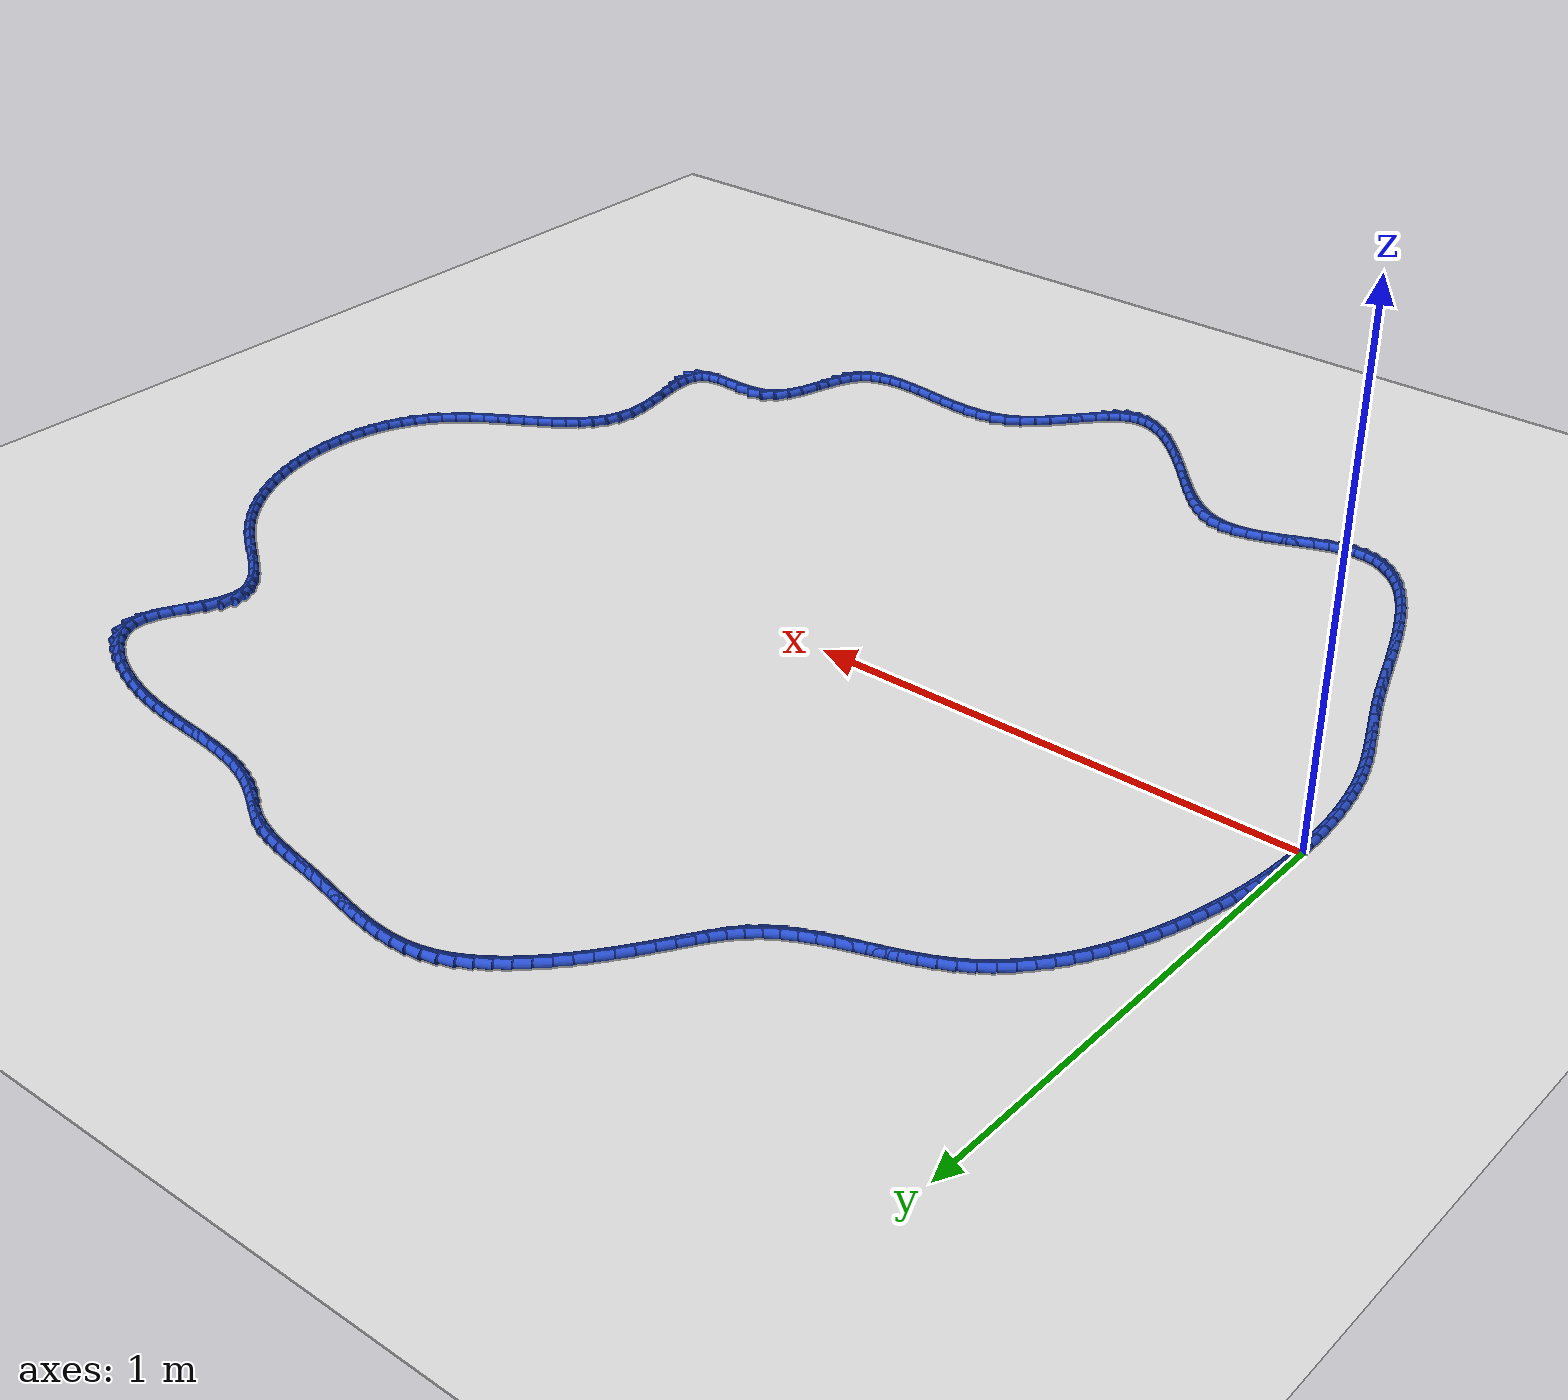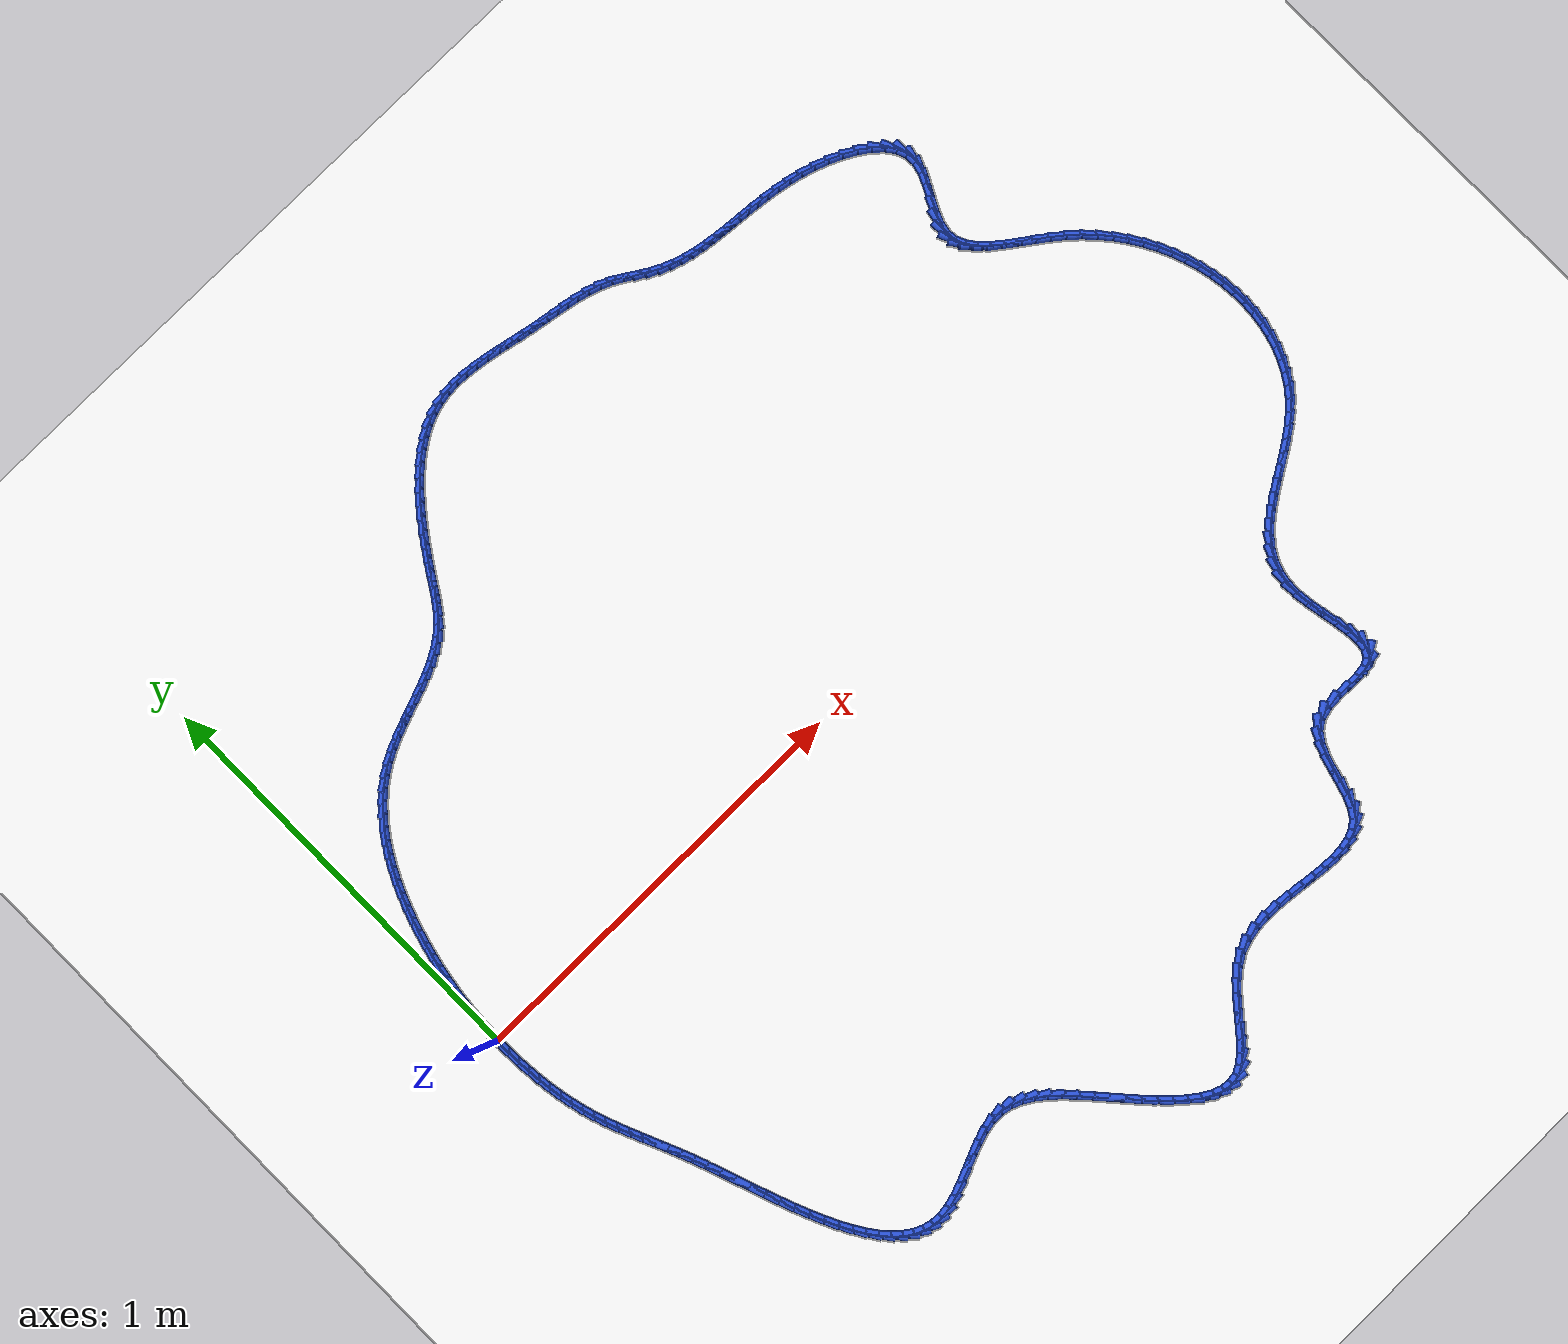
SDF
<sdf version="1.6">
 <world name="default">
  <light name="sun" type="directional">
   <pose>0 0 10 0 -0 0</pose>
   <diffuse>0.8 0.8 0.8 1</diffuse>
   <specular>0.2 0.2 0.2 1</specular>
   <attenuation>
    <range>1000</range>
    <constant>0.9</constant>
    <linear>0.01</linear>
    <quadratic>0.001</quadratic>
   </attenuation>
   <direction>-0.5 0.1 -0.9</direction>
  </light>
  <model name="ground_plane">
   <static>1</static>
   <link name="link">
    <collision name="collision">
     <geometry><plane><normal>0 0 1</normal><size>100 100</size></plane></geometry>
     <surface><friction><ode><mu>100</mu><mu2>50</mu2></ode></friction></surface>
    </collision>
    <visual name="visual">
     <cast_shadows>0</cast_shadows>
     <geometry><plane><normal>0 0 1</normal><size>100 100</size></plane></geometry>
     <material>
      <script><uri>file://media/materials/scripts/gazebo.material</uri><name>Gazebo/WhiteGlow</name></script>
     </material>
    </visual>
   </link>
  </model>
  <gravity>0 0 -9.8</gravity>
  <magnetic_field>6e-06 2.3e-05 -4.2e-05</magnetic_field>
  <atmosphere type="adiabatic"/>
  <physics name="default_physics" default="0" type="ode">
   <max_step_size>0.001</max_step_size>
   <real_time_factor>1</real_time_factor>
   <real_time_update_rate>1000</real_time_update_rate>
  </physics>
  <scene><ambient>0.4 0.4 0.4 1</ambient><background>0.7 0.7 0.7 1</background><shadows>1</shadows></scene>
  <spherical_coordinates>
   <surface_model>EARTH_WGS84</surface_model>
   <latitude_deg>0</latitude_deg>
   <longitude_deg>0</longitude_deg>
   <elevation>0</elevation>
   <heading_deg>0</heading_deg>
  </spherical_coordinates>
  <model name="line">
   <link name="link_0">
    <pose>2.168404344971009e-18 -6.938893903907228e-18 0.01 0 1.57 1.552432151949508</pose>
    <collision name="collision">
     <geometry><cylinder><radius>0.01</radius><length>0.08</length></cylinder></geometry>
    </collision>
    <visual name="visual">
     <material>
      <script><name>Gazebo/Blue</name><uri>file://media/materials/scripts/gazebo.material</uri></script>
     </material>
     <geometry><cylinder><radius>0.01</radius><length>0.08</length></cylinder></geometry>
    </visual>
   </link>
   <link name="link_1">
    <pose>0.0005430636565950811 0.02956858185407783 0.01 0 1.57 1.5245968007028479</pose>
    <collision name="collision">
     <geometry><cylinder><radius>0.01</radius><length>0.08</length></cylinder></geometry>
    </collision>
    <visual name="visual">
     <material>
      <script><name>Gazebo/Blue</name><uri>file://media/materials/scripts/gazebo.material</uri></script>
     </material>
     <geometry><cylinder><radius>0.01</radius><length>0.08</length></cylinder></geometry>
    </visual>
   </link>
   <link name="link_2">
    <pose>0.001901446916020607 0.058950196645555515 0.01 0 1.57 1.4962083804458244</pose>
    <collision name="collision">
     <geometry><cylinder><radius>0.01</radius><length>0.08</length></cylinder></geometry>
    </collision>
    <visual name="visual">
     <material>
      <script><name>Gazebo/Blue</name><uri>file://media/materials/scripts/gazebo.material</uri></script>
     </material>
     <geometry><cylinder><radius>0.01</radius><length>0.08</length></cylinder></geometry>
    </visual>
   </link>
   <link name="link_3">
    <pose>0.004086540318610927 0.08819137904341232 0.01 0 1.57 1.4674445983608793</pose>
    <collision name="collision">
     <geometry><cylinder><radius>0.01</radius><length>0.08</length></cylinder></geometry>
    </collision>
    <visual name="visual">
     <material>
      <script><name>Gazebo/Blue</name><uri>file://media/materials/scripts/gazebo.material</uri></script>
     </material>
     <geometry><cylinder><radius>0.01</radius><length>0.08</length></cylinder></geometry>
    </visual>
   </link>
   <link name="link_4">
    <pose>0.007109734404700387 0.11733866371662746 0.01 0 1.57 1.438491423683931</pose>
    <collision name="collision">
     <geometry><cylinder><radius>0.01</radius><length>0.08</length></cylinder></geometry>
    </collision>
    <visual name="visual">
     <material>
      <script><name>Gazebo/Blue</name><uri>file://media/materials/scripts/gazebo.material</uri></script>
     </material>
     <geometry><cylinder><radius>0.01</radius><length>0.08</length></cylinder></geometry>
    </visual>
   </link>
   <link name="link_5">
    <pose>0.010982419714623335 0.14643858533418017 0.01 0 1.57 1.409538211780621</pose>
    <collision name="collision">
     <geometry><cylinder><radius>0.01</radius><length>0.08</length></cylinder></geometry>
    </collision>
    <visual name="visual">
     <material>
      <script><name>Gazebo/Blue</name><uri>file://media/materials/scripts/gazebo.material</uri></script>
     </material>
     <geometry><cylinder><radius>0.01</radius><length>0.08</length></cylinder></geometry>
    </visual>
   </link>
   <link name="link_6">
    <pose>0.015715986788714113 0.17553767856504965 0.01 0 1.57 1.3807726272057732</pose>
    <collision name="collision">
     <geometry><cylinder><radius>0.01</radius><length>0.08</length></cylinder></geometry>
    </collision>
    <visual name="visual">
     <material>
      <script><name>Gazebo/Blue</name><uri>file://media/materials/scripts/gazebo.material</uri></script>
     </material>
     <geometry><cylinder><radius>0.01</radius><length>0.08</length></cylinder></geometry>
    </visual>
   </link>
   <link name="link_7">
    <pose>0.021321826167307073 0.2046824780782151 0.01 0 1.57 1.3523756889447778</pose>
    <collision name="collision">
     <geometry><cylinder><radius>0.01</radius><length>0.08</length></cylinder></geometry>
    </collision>
    <visual name="visual">
     <material>
      <script><name>Gazebo/Blue</name><uri>file://media/materials/scripts/gazebo.material</uri></script>
     </material>
     <geometry><cylinder><radius>0.01</radius><length>0.08</length></cylinder></geometry>
    </visual>
   </link>
   <link name="link_8">
    <pose>0.02781132839073656 0.23391951854265577 0.01 0 1.57 1.3244591229529863</pose>
    <collision name="collision">
     <geometry><cylinder><radius>0.01</radius><length>0.08</length></cylinder></geometry>
    </collision>
    <visual name="visual">
     <material>
      <script><name>Gazebo/Blue</name><uri>file://media/materials/scripts/gazebo.material</uri></script>
     </material>
     <geometry><cylinder><radius>0.01</radius><length>0.08</length></cylinder></geometry>
    </visual>
   </link>
   <link name="link_9">
    <pose>0.03519663869131008 0.2632911163498984 0.01 0 1.57 1.2957435349868862</pose>
    <collision name="collision">
     <geometry><cylinder><radius>0.01</radius><length>0.08</length></cylinder></geometry>
    </collision>
    <visual name="visual">
     <material>
      <script><name>Gazebo/Blue</name><uri>file://media/materials/scripts/gazebo.material</uri></script>
     </material>
     <geometry><cylinder><radius>0.01</radius><length>0.08</length></cylinder></geometry>
    </visual>
   </link>
   <link name="link_10">
    <pose>0.04350754858759399 0.29274095568907144 0.01 0 1.57 1.2646491216527687</pose>
    <collision name="collision">
     <geometry><cylinder><radius>0.01</radius><length>0.08</length></cylinder></geometry>
    </collision>
    <visual name="visual">
     <material>
      <script><name>Gazebo/Blue</name><uri>file://media/materials/scripts/gazebo.material</uri></script>
     </material>
     <geometry><cylinder><radius>0.01</radius><length>0.08</length></cylinder></geometry>
    </visual>
   </link>
   <link name="link_11">
    <pose>0.05279165759298627 0.3221131846925495 0.01 0 1.57 1.2308025997931469</pose>
    <collision name="collision">
     <geometry><cylinder><radius>0.01</radius><length>0.08</length></cylinder></geometry>
    </collision>
    <visual name="visual">
     <material>
      <script><name>Gazebo/Blue</name><uri>file://media/materials/scripts/gazebo.material</uri></script>
     </material>
     <geometry><cylinder><radius>0.01</radius><length>0.08</length></cylinder></geometry>
    </visual>
   </link>
   <link name="link_12">
    <pose>0.06309735225541638 0.3512475524396692 0.01 0 1.57 1.1938600088988178</pose>
    <collision name="collision">
     <geometry><cylinder><radius>0.01</radius><length>0.08</length></cylinder></geometry>
    </collision>
    <visual name="visual">
     <material>
      <script><name>Gazebo/Blue</name><uri>file://media/materials/scripts/gazebo.material</uri></script>
     </material>
     <geometry><cylinder><radius>0.01</radius><length>0.08</length></cylinder></geometry>
    </visual>
   </link>
   <link name="link_13">
    <pose>0.07447301912281365 0.3799838080097663 0.01 0 1.57 1.1534460394575619</pose>
    <collision name="collision">
     <geometry><cylinder><radius>0.01</radius><length>0.08</length></cylinder></geometry>
    </collision>
    <visual name="visual">
     <material>
      <script><name>Gazebo/Blue</name><uri>file://media/materials/scripts/gazebo.material</uri></script>
     </material>
     <geometry><cylinder><radius>0.01</radius><length>0.08</length></cylinder></geometry>
    </visual>
   </link>
   <link name="link_14">
    <pose>0.08696704474310744 0.4081617004821769 0.01 0 1.57 1.1091571426501097</pose>
    <collision name="collision">
     <geometry><cylinder><radius>0.01</radius><length>0.08</length></cylinder></geometry>
    </collision>
    <visual name="visual">
     <material>
      <script><name>Gazebo/Blue</name><uri>file://media/materials/scripts/gazebo.material</uri></script>
     </material>
     <geometry><cylinder><radius>0.01</radius><length>0.08</length></cylinder></geometry>
    </visual>
   </link>
   <link name="link_15">
    <pose>0.10062781566422715 0.435620978936237 0.01 0 1.57 1.0605694932200733</pose>
    <collision name="collision">
     <geometry><cylinder><radius>0.01</radius><length>0.08</length></cylinder></geometry>
    </collision>
    <visual name="visual">
     <material>
      <script><name>Gazebo/Blue</name><uri>file://media/materials/scripts/gazebo.material</uri></script>
     </material>
     <geometry><cylinder><radius>0.01</radius><length>0.08</length></cylinder></geometry>
    </visual>
   </link>
   <link name="link_16">
    <pose>0.11550371843410225 0.4622013924512831 0.01 0 1.57 1.0072540861359254</pose>
    <collision name="collision">
     <geometry><cylinder><radius>0.01</radius><length>0.08</length></cylinder></geometry>
    </collision>
    <visual name="visual">
     <material>
      <script><name>Gazebo/Blue</name><uri>file://media/materials/scripts/gazebo.material</uri></script>
     </material>
     <geometry><cylinder><radius>0.01</radius><length>0.08</length></cylinder></geometry>
    </visual>
   </link>
   <link name="link_17">
    <pose>0.13164313960066198 0.4877426901066507 0.01 0 1.57 0.9488017304271342</pose>
    <collision name="collision">
     <geometry><cylinder><radius>0.01</radius><length>0.08</length></cylinder></geometry>
    </collision>
    <visual name="visual">
     <material>
      <script><name>Gazebo/Blue</name><uri>file://media/materials/scripts/gazebo.material</uri></script>
     </material>
     <geometry><cylinder><radius>0.01</radius><length>0.08</length></cylinder></geometry>
    </visual>
   </link>
   <link name="link_18">
    <pose>0.1490944657118359 0.5120846209816764 0.01 0 1.57 0.8848607675296601</pose>
    <collision name="collision">
     <geometry><cylinder><radius>0.01</radius><length>0.08</length></cylinder></geometry>
    </collision>
    <visual name="visual">
     <material>
      <script><name>Gazebo/Blue</name><uri>file://media/materials/scripts/gazebo.material</uri></script>
     </material>
     <geometry><cylinder><radius>0.01</radius><length>0.08</length></cylinder></geometry>
    </visual>
   </link>
   <link name="link_19">
    <pose>0.1679060833155531 0.5350669341556955 0.01 0 1.57 0.8151894248052729</pose>
    <collision name="collision">
     <geometry><cylinder><radius>0.01</radius><length>0.08</length></cylinder></geometry>
    </collision>
    <visual name="visual">
     <material>
      <script><name>Gazebo/Blue</name><uri>file://media/materials/scripts/gazebo.material</uri></script>
     </material>
     <geometry><cylinder><radius>0.01</radius><length>0.08</length></cylinder></geometry>
    </visual>
   </link>
   <link name="link_20">
    <pose>0.18812637895974327 0.556529378708045 0.01 0 1.57 0.7397220529052339</pose>
    <collision name="collision">
     <geometry><cylinder><radius>0.01</radius><length>0.08</length></cylinder></geometry>
    </collision>
    <visual name="visual">
     <material>
      <script><name>Gazebo/Blue</name><uri>file://media/materials/scripts/gazebo.material</uri></script>
     </material>
     <geometry><cylinder><radius>0.01</radius><length>0.08</length></cylinder></geometry>
    </visual>
   </link>
   <link name="link_21">
    <pose>0.20980373919233566 0.5763117037180603 0.01 0 1.57 0.658643427475</pose>
    <collision name="collision">
     <geometry><cylinder><radius>0.01</radius><length>0.08</length></cylinder></geometry>
    </collision>
    <visual name="visual">
     <material>
      <script><name>Gazebo/Blue</name><uri>file://media/materials/scripts/gazebo.material</uri></script>
     </material>
     <geometry><cylinder><radius>0.01</radius><length>0.08</length></cylinder></geometry>
    </visual>
   </link>
   <link name="link_22">
    <pose>0.2329865505612596 0.5942536582650778 0.01 0 1.57 0.5725282802318538</pose>
    <collision name="collision">
     <geometry><cylinder><radius>0.01</radius><length>0.08</length></cylinder></geometry>
    </collision>
    <visual name="visual">
     <material>
      <script><name>Gazebo/Blue</name><uri>file://media/materials/scripts/gazebo.material</uri></script>
     </material>
     <geometry><cylinder><radius>0.01</radius><length>0.08</length></cylinder></geometry>
    </visual>
   </link>
   <link name="link_23">
    <pose>0.25772204115448405 0.6101967047606794 0.01 0 1.57 0.4901279271366909</pose>
    <collision name="collision">
     <geometry><cylinder><radius>0.01</radius><length>0.08</length></cylinder></geometry>
    </collision>
    <visual name="visual">
     <material>
      <script><name>Gazebo/Blue</name><uri>file://media/materials/scripts/gazebo.material</uri></script>
     </material>
     <geometry><cylinder><radius>0.01</radius><length>0.08</length></cylinder></geometry>
    </visual>
   </link>
   <link name="link_24">
    <pose>0.2839254079945096 0.6241775761390692 0.01 0 1.57 0.4267393349831475</pose>
    <collision name="collision">
     <geometry><cylinder><radius>0.01</radius><length>0.08</length></cylinder></geometry>
    </collision>
    <visual name="visual">
     <material>
      <script><name>Gazebo/Blue</name><uri>file://media/materials/scripts/gazebo.material</uri></script>
     </material>
     <geometry><cylinder><radius>0.01</radius><length>0.08</length></cylinder></geometry>
    </visual>
   </link>
   <link name="link_25">
    <pose>0.31125969098995054 0.6366059391681403 0.01 0 1.57 0.3831897071688424</pose>
    <collision name="collision">
     <geometry><cylinder><radius>0.01</radius><length>0.08</length></cylinder></geometry>
    </collision>
    <visual name="visual">
     <material>
      <script><name>Gazebo/Blue</name><uri>file://media/materials/scripts/gazebo.material</uri></script>
     </material>
     <geometry><cylinder><radius>0.01</radius><length>0.08</length></cylinder></geometry>
    </visual>
   </link>
   <link name="link_26">
    <pose>0.3393595455488783 0.6479334405561584 0.01 0 1.57 0.3584862747002532</pose>
    <collision name="collision">
     <geometry><cylinder><radius>0.01</radius><length>0.08</length></cylinder></geometry>
    </collision>
    <visual name="visual">
     <material>
      <script><name>Gazebo/Blue</name><uri>file://media/materials/scripts/gazebo.material</uri></script>
     </material>
     <geometry><cylinder><radius>0.01</radius><length>0.08</length></cylinder></geometry>
    </visual>
   </link>
   <link name="link_27">
    <pose>0.36785962707936376 0.6586117270113878 0.01 0 1.57 0.35199758253719793</pose>
    <collision name="collision">
     <geometry><cylinder><radius>0.01</radius><length>0.08</length></cylinder></geometry>
    </collision>
    <visual name="visual">
     <material>
      <script><name>Gazebo/Blue</name><uri>file://media/materials/scripts/gazebo.material</uri></script>
     </material>
     <geometry><cylinder><radius>0.01</radius><length>0.08</length></cylinder></geometry>
    </visual>
   </link>
   <link name="link_28">
    <pose>0.3963945909894785 0.6690924452420933 0.01 0 1.57 0.363676257050509</pose>
    <collision name="collision">
     <geometry><cylinder><radius>0.01</radius><length>0.08</length></cylinder></geometry>
    </collision>
    <visual name="visual">
     <material>
      <script><name>Gazebo/Blue</name><uri>file://media/materials/scripts/gazebo.material</uri></script>
     </material>
     <geometry><cylinder><radius>0.01</radius><length>0.08</length></cylinder></geometry>
    </visual>
   </link>
   <link name="link_29">
    <pose>0.42459909268729357 0.6798272419565402 0.01 0 1.57 0.39412701709626485</pose>
    <collision name="collision">
     <geometry><cylinder><radius>0.01</radius><length>0.08</length></cylinder></geometry>
    </collision>
    <visual name="visual">
     <material>
      <script><name>Gazebo/Blue</name><uri>file://media/materials/scripts/gazebo.material</uri></script>
     </material>
     <geometry><cylinder><radius>0.01</radius><length>0.08</length></cylinder></geometry>
    </visual>
   </link>
   <link name="link_30">
    <pose>0.45210778758088016 0.6912677638629928 0.01 0 1.57 0.4445371107475938</pose>
    <collision name="collision">
     <geometry><cylinder><radius>0.01</radius><length>0.08</length></cylinder></geometry>
    </collision>
    <visual name="visual">
     <material>
      <script><name>Gazebo/Blue</name><uri>file://media/materials/scripts/gazebo.material</uri></script>
     </material>
     <geometry><cylinder><radius>0.01</radius><length>0.08</length></cylinder></geometry>
    </visual>
   </link>
   <link name="link_31">
    <pose>0.4785553310783092 0.7038656576697161 0.01 0 1.57 0.5164052948168326</pose>
    <collision name="collision">
     <geometry><cylinder><radius>0.01</radius><length>0.08</length></cylinder></geometry>
    </collision>
    <visual name="visual">
     <material>
      <script><name>Gazebo/Blue</name><uri>file://media/materials/scripts/gazebo.material</uri></script>
     </material>
     <geometry><cylinder><radius>0.01</radius><length>0.08</length></cylinder></geometry>
    </visual>
   </link>
   <link name="link_32">
    <pose>0.5035763785876523 0.718072570084975 0.01 0 1.57 0.6109320187012139</pose>
    <collision name="collision">
     <geometry><cylinder><radius>0.01</radius><length>0.08</length></cylinder></geometry>
    </collision>
    <visual name="visual">
     <material>
      <script><name>Gazebo/Blue</name><uri>file://media/materials/scripts/gazebo.material</uri></script>
     </material>
     <geometry><cylinder><radius>0.01</radius><length>0.08</length></cylinder></geometry>
    </visual>
   </link>
   <link name="link_33">
    <pose>0.5268055855169804 0.7343401478170343 0.01 0 1.57 0.7276663670533404</pose>
    <collision name="collision">
     <geometry><cylinder><radius>0.01</radius><length>0.08</length></cylinder></geometry>
    </collision>
    <visual name="visual">
     <material>
      <script><name>Gazebo/Blue</name><uri>file://media/materials/scripts/gazebo.material</uri></script>
     </material>
     <geometry><cylinder><radius>0.01</radius><length>0.08</length></cylinder></geometry>
    </visual>
   </link>
   <link name="link_34">
    <pose>0.5478832615185447 0.7531145332309316 0.01 0 1.57 0.845127359304378</pose>
    <collision name="collision">
     <geometry><cylinder><radius>0.01</radius><length>0.08</length></cylinder></geometry>
    </collision>
    <visual name="visual">
     <material>
      <script><name>Gazebo/Blue</name><uri>file://media/materials/scripts/gazebo.material</uri></script>
     </material>
     <geometry><cylinder><radius>0.01</radius><length>0.08</length></cylinder></geometry>
    </visual>
   </link>
   <link name="link_35">
    <pose>0.5668301064734417 0.7744715630746686 0.01 0 1.57 0.9303539195746711</pose>
    <collision name="collision">
     <geometry><cylinder><radius>0.01</radius><length>0.08</length></cylinder></geometry>
    </collision>
    <visual name="visual">
     <material>
      <script><name>Gazebo/Blue</name><uri>file://media/materials/scripts/gazebo.material</uri></script>
     </material>
     <geometry><cylinder><radius>0.01</radius><length>0.08</length></cylinder></geometry>
    </visual>
   </link>
   <link name="link_36">
    <pose>0.584281379478836 0.7978888075992316 0.01 0 1.57 0.9815036223953305</pose>
    <collision name="collision">
     <geometry><cylinder><radius>0.01</radius><length>0.08</length></cylinder></geometry>
    </collision>
    <visual name="visual">
     <material>
      <script><name>Gazebo/Blue</name><uri>file://media/materials/scripts/gazebo.material</uri></script>
     </material>
     <geometry><cylinder><radius>0.01</radius><length>0.08</length></cylinder></geometry>
    </visual>
   </link>
   <link name="link_37">
    <pose>0.6009282330927199 0.8227894253990211 0.01 0 1.57 1.001015654956713</pose>
    <collision name="collision">
     <geometry><cylinder><radius>0.01</radius><length>0.08</length></cylinder></geometry>
    </collision>
    <visual name="visual">
     <material>
      <script><name>Gazebo/Blue</name><uri>file://media/materials/scripts/gazebo.material</uri></script>
     </material>
     <geometry><cylinder><radius>0.01</radius><length>0.08</length></cylinder></geometry>
    </visual>
   </link>
   <link name="link_38">
    <pose>0.6174618198730861 0.8485965750684389 0.01 0 1.57 0.9932530872668094</pose>
    <collision name="collision">
     <geometry><cylinder><radius>0.01</radius><length>0.08</length></cylinder></geometry>
    </collision>
    <visual name="visual">
     <material>
      <script><name>Gazebo/Blue</name><uri>file://media/materials/scripts/gazebo.material</uri></script>
     </material>
     <geometry><cylinder><radius>0.01</radius><length>0.08</length></cylinder></geometry>
    </visual>
   </link>
   <link name="link_39">
    <pose>0.6345118933357509 0.8747605271081191 0.01 0 1.57 0.9742703240293497</pose>
    <collision name="collision">
     <geometry><cylinder><radius>0.01</radius><length>0.08</length></cylinder></geometry>
    </collision>
    <visual name="visual">
     <material>
      <script><name>Gazebo/Blue</name><uri>file://media/materials/scripts/gazebo.material</uri></script>
     </material>
     <geometry><cylinder><radius>0.01</radius><length>0.08</length></cylinder></geometry>
    </visual>
   </link>
   <link name="link_40">
    <pose>0.6522768348717717 0.9009220325243141 0.01 0 1.57 0.950379968052218</pose>
    <collision name="collision">
     <geometry><cylinder><radius>0.01</radius><length>0.08</length></cylinder></geometry>
    </collision>
    <visual name="visual">
     <material>
      <script><name>Gazebo/Blue</name><uri>file://media/materials/scripts/gazebo.material</uri></script>
     </material>
     <geometry><cylinder><radius>0.01</radius><length>0.08</length></cylinder></geometry>
    </visual>
   </link>
   <link name="link_41">
    <pose>0.6707701155462291 0.9268034929686579 0.01 0 1.57 0.9212251369995517</pose>
    <collision name="collision">
     <geometry><cylinder><radius>0.01</radius><length>0.08</length></cylinder></geometry>
    </collision>
    <visual name="visual">
     <material>
      <script><name>Gazebo/Blue</name><uri>file://media/materials/scripts/gazebo.material</uri></script>
     </material>
     <geometry><cylinder><radius>0.01</radius><length>0.08</length></cylinder></geometry>
    </visual>
   </link>
   <link name="link_42">
    <pose>0.6900045003930402 0.952127621854173 0.01 0 1.57 0.886257171846534</pose>
    <collision name="collision">
     <geometry><cylinder><radius>0.01</radius><length>0.08</length></cylinder></geometry>
    </collision>
    <visual name="visual">
     <material>
      <script><name>Gazebo/Blue</name><uri>file://media/materials/scripts/gazebo.material</uri></script>
     </material>
     <geometry><cylinder><radius>0.01</radius><length>0.08</length></cylinder></geometry>
    </visual>
   </link>
   <link name="link_43">
    <pose>0.709992754446123 0.9766171325938823 0.01 0 1.57 0.8447566182954042</pose>
    <collision name="collision">
     <geometry><cylinder><radius>0.01</radius><length>0.08</length></cylinder></geometry>
    </collision>
    <visual name="visual">
     <material>
      <script><name>Gazebo/Blue</name><uri>file://media/materials/scripts/gazebo.material</uri></script>
     </material>
     <geometry><cylinder><radius>0.01</radius><length>0.08</length></cylinder></geometry>
    </visual>
   </link>
   <link name="link_44">
    <pose>0.7307476427393947 0.9999947386008087 0.01 0 1.57 0.7958320431084995</pose>
    <collision name="collision">
     <geometry><cylinder><radius>0.01</radius><length>0.08</length></cylinder></geometry>
    </collision>
    <visual name="visual">
     <material>
      <script><name>Gazebo/Blue</name><uri>file://media/materials/scripts/gazebo.material</uri></script>
     </material>
     <geometry><cylinder><radius>0.01</radius><length>0.08</length></cylinder></geometry>
    </visual>
   </link>
   <link name="link_45">
    <pose>0.7522819303067732 1.0219831532879748 0.01 0 1.57 0.7384317700576108</pose>
    <collision name="collision">
     <geometry><cylinder><radius>0.01</radius><length>0.08</length></cylinder></geometry>
    </collision>
    <visual name="visual">
     <material>
      <script><name>Gazebo/Blue</name><uri>file://media/materials/scripts/gazebo.material</uri></script>
     </material>
     <geometry><cylinder><radius>0.01</radius><length>0.08</length></cylinder></geometry>
    </visual>
   </link>
   <link name="link_46">
    <pose>0.774608382182176 1.0423050900684043 0.01 0 1.57 0.6713859577516702</pose>
    <collision name="collision">
     <geometry><cylinder><radius>0.01</radius><length>0.08</length></cylinder></geometry>
    </collision>
    <visual name="visual">
     <material>
      <script><name>Gazebo/Blue</name><uri>file://media/materials/scripts/gazebo.material</uri></script>
     </material>
     <geometry><cylinder><radius>0.01</radius><length>0.08</length></cylinder></geometry>
    </visual>
   </link>
   <link name="link_47">
    <pose>0.7977397633995207 1.0606832623551194 0.01 0 1.57 0.5935056619220203</pose>
    <collision name="collision">
     <geometry><cylinder><radius>0.01</radius><length>0.08</length></cylinder></geometry>
    </collision>
    <visual name="visual">
     <material>
      <script><name>Gazebo/Blue</name><uri>file://media/materials/scripts/gazebo.material</uri></script>
     </material>
     <geometry><cylinder><radius>0.01</radius><length>0.08</length></cylinder></geometry>
    </visual>
   </link>
   <link name="link_48">
    <pose>0.8216888389927248 1.0768403835611435 0.01 0 1.57 0.5037734537976285</pose>
    <collision name="collision">
     <geometry><cylinder><radius>0.01</radius><length>0.08</length></cylinder></geometry>
    </collision>
    <visual name="visual">
     <material>
      <script><name>Gazebo/Blue</name><uri>file://media/materials/scripts/gazebo.material</uri></script>
     </material>
     <geometry><cylinder><radius>0.01</radius><length>0.08</length></cylinder></geometry>
    </visual>
   </link>
   <link name="link_49">
    <pose>0.8464683739957058 1.0904991670994986 0.01 0 1.57 0.40165531224368434</pose>
    <collision name="collision">
     <geometry><cylinder><radius>0.01</radius><length>0.08</length></cylinder></geometry>
    </collision>
    <visual name="visual">
     <material>
      <script><name>Gazebo/Blue</name><uri>file://media/materials/scripts/gazebo.material</uri></script>
     </material>
     <geometry><cylinder><radius>0.01</radius><length>0.08</length></cylinder></geometry>
    </visual>
   </link>
   <link name="link_50">
    <pose>0.8720911334423816 1.1013823263832083 0.01 0 1.57 0.28752393944200116</pose>
    <collision name="collision">
     <geometry><cylinder><radius>0.01</radius><length>0.08</length></cylinder></geometry>
    </collision>
    <visual name="visual">
     <material>
      <script><name>Gazebo/Blue</name><uri>file://media/materials/scripts/gazebo.material</uri></script>
     </material>
     <geometry><cylinder><radius>0.01</radius><length>0.08</length></cylinder></geometry>
    </visual>
   </link>
   <link name="link_51">
    <pose>0.8985698823666695 1.1092125748252952 0.01 0 1.57 0.16746332577175901</pose>
    <collision name="collision">
     <geometry><cylinder><radius>0.01</radius><length>0.08</length></cylinder></geometry>
    </collision>
    <visual name="visual">
     <material>
      <script><name>Gazebo/Blue</name><uri>file://media/materials/scripts/gazebo.material</uri></script>
     </material>
     <geometry><cylinder><radius>0.01</radius><length>0.08</length></cylinder></geometry>
    </visual>
   </link>
   <link name="link_52">
    <pose>0.9258967491045006 1.113832086909286 0.01 0 1.57 0.06163201362966509</pose>
    <collision name="collision">
     <geometry><cylinder><radius>0.01</radius><length>0.08</length></cylinder></geometry>
    </collision>
    <visual name="visual">
     <material>
      <script><name>Gazebo/Blue</name><uri>file://media/materials/scripts/gazebo.material</uri></script>
     </material>
     <geometry><cylinder><radius>0.01</radius><length>0.08</length></cylinder></geometry>
    </visual>
   </link>
   <link name="link_53">
    <pose>0.9539805787087852 1.1155651447771653 0.01 0 1.57 -0.02462243923433785</pose>
    <collision name="collision">
     <geometry><cylinder><radius>0.01</radius><length>0.08</length></cylinder></geometry>
    </collision>
    <visual name="visual">
     <material>
      <script><name>Gazebo/Blue</name><uri>file://media/materials/scripts/gazebo.material</uri></script>
     </material>
     <geometry><cylinder><radius>0.01</radius><length>0.08</length></cylinder></geometry>
    </visual>
   </link>
   <link name="link_54">
    <pose>0.9827092096491266 1.1148576328219746 0.01 0 1.57 -0.09208605516539609</pose>
    <collision name="collision">
     <geometry><cylinder><radius>0.01</radius><length>0.08</length></cylinder></geometry>
    </collision>
    <visual name="visual">
     <material>
      <script><name>Gazebo/Blue</name><uri>file://media/materials/scripts/gazebo.material</uri></script>
     </material>
     <geometry><cylinder><radius>0.01</radius><length>0.08</length></cylinder></geometry>
    </visual>
   </link>
   <link name="link_55">
    <pose>1.0119704803945873 1.1121554354398833 0.01 0 1.57 -0.1422519207330489</pose>
    <collision name="collision">
     <geometry><cylinder><radius>0.01</radius><length>0.08</length></cylinder></geometry>
    </collision>
    <visual name="visual">
     <material>
      <script><name>Gazebo/Blue</name><uri>file://media/materials/scripts/gazebo.material</uri></script>
     </material>
     <geometry><cylinder><radius>0.01</radius><length>0.08</length></cylinder></geometry>
    </visual>
   </link>
   <link name="link_56">
    <pose>1.04165222941423 1.1079044370270599 0.01 0 1.57 -0.1766618763921665</pose>
    <collision name="collision">
     <geometry><cylinder><radius>0.01</radius><length>0.08</length></cylinder></geometry>
    </collision>
    <visual name="visual">
     <material>
      <script><name>Gazebo/Blue</name><uri>file://media/materials/scripts/gazebo.material</uri></script>
     </material>
     <geometry><cylinder><radius>0.01</radius><length>0.08</length></cylinder></geometry>
    </visual>
   </link>
   <link name="link_57">
    <pose>1.0716422951771174 1.102550521979675 0.01 0 1.57 -0.19655776963537325</pose>
    <collision name="collision">
     <geometry><cylinder><radius>0.01</radius><length>0.08</length></cylinder></geometry>
    </collision>
    <visual name="visual">
     <material>
      <script><name>Gazebo/Blue</name><uri>file://media/materials/scripts/gazebo.material</uri></script>
     </material>
     <geometry><cylinder><radius>0.01</radius><length>0.08</length></cylinder></geometry>
    </visual>
   </link>
   <link name="link_58">
    <pose>1.101828516152312 1.0965395746938977 0.01 0 1.57 -0.2027280223977942</pose>
    <collision name="collision">
     <geometry><cylinder><radius>0.01</radius><length>0.08</length></cylinder></geometry>
    </collision>
    <visual name="visual">
     <material>
      <script><name>Gazebo/Blue</name><uri>file://media/materials/scripts/gazebo.material</uri></script>
     </material>
     <geometry><cylinder><radius>0.01</radius><length>0.08</length></cylinder></geometry>
    </visual>
   </link>
   <link name="link_59">
    <pose>1.1320987308088764 1.090317479565897 0.01 0 1.57 -0.1954537136168871</pose>
    <collision name="collision">
     <geometry><cylinder><radius>0.01</radius><length>0.08</length></cylinder></geometry>
    </collision>
    <visual name="visual">
     <material>
      <script><name>Gazebo/Blue</name><uri>file://media/materials/scripts/gazebo.material</uri></script>
     </material>
     <geometry><cylinder><radius>0.01</radius><length>0.08</length></cylinder></geometry>
    </visual>
   </link>
   <link name="link_60">
    <pose>1.1623407776158725 1.0843301209918426 0.01 0 1.57 -0.17618737623844744</pose>
    <collision name="collision">
     <geometry><cylinder><radius>0.01</radius><length>0.08</length></cylinder></geometry>
    </collision>
    <visual name="visual">
     <material>
      <script><name>Gazebo/Blue</name><uri>file://media/materials/scripts/gazebo.material</uri></script>
     </material>
     <geometry><cylinder><radius>0.01</radius><length>0.08</length></cylinder></geometry>
    </visual>
   </link>
   <link name="link_61">
    <pose>1.1924422514113204 1.0789710541708346 0.01 0 1.57 -0.16349710700885836</pose>
    <collision name="collision">
     <geometry><cylinder><radius>0.01</radius><length>0.08</length></cylinder></geometry>
    </collision>
    <visual name="visual">
     <material>
      <script><name>Gazebo/Blue</name><uri>file://media/materials/scripts/gazebo.material</uri></script>
     </material>
     <geometry><cylinder><radius>0.01</radius><length>0.08</length></cylinder></geometry>
    </visual>
   </link>
   <link name="link_62">
    <pose>1.2222880167843102 1.0740474076623578 0.01 0 1.57 -0.16967087327609182</pose>
    <collision name="collision">
     <geometry><cylinder><radius>0.01</radius><length>0.08</length></cylinder></geometry>
    </collision>
    <visual name="visual">
     <material>
      <script><name>Gazebo/Blue</name><uri>file://media/materials/scripts/gazebo.material</uri></script>
     </material>
     <geometry><cylinder><radius>0.01</radius><length>0.08</length></cylinder></geometry>
    </visual>
   </link>
   <link name="link_63">
    <pose>1.2517612241100597 1.068998116243236 0.01 0 1.57 -0.19556838650483138</pose>
    <collision name="collision">
     <geometry><cylinder><radius>0.01</radius><length>0.08</length></cylinder></geometry>
    </collision>
    <visual name="visual">
     <material>
      <script><name>Gazebo/Blue</name><uri>file://media/materials/scripts/gazebo.material</uri></script>
     </material>
     <geometry><cylinder><radius>0.01</radius><length>0.08</length></cylinder></geometry>
    </visual>
   </link>
   <link name="link_64">
    <pose>1.2807449972427511 1.0632564182711728 0.01 0 1.57 -0.24187523023586457</pose>
    <collision name="collision">
     <geometry><cylinder><radius>0.01</radius><length>0.08</length></cylinder></geometry>
    </collision>
    <visual name="visual">
     <material>
      <script><name>Gazebo/Blue</name><uri>file://media/materials/scripts/gazebo.material</uri></script>
     </material>
     <geometry><cylinder><radius>0.01</radius><length>0.08</length></cylinder></geometry>
    </visual>
   </link>
   <link name="link_65">
    <pose>1.3091224600365663 1.0562555521038728 0.01 0 1.57 -0.3089623519939928</pose>
    <collision name="collision">
     <geometry><cylinder><radius>0.01</radius><length>0.08</length></cylinder></geometry>
    </collision>
    <visual name="visual">
     <material>
      <script><name>Gazebo/Blue</name><uri>file://media/materials/scripts/gazebo.material</uri></script>
     </material>
     <geometry><cylinder><radius>0.01</radius><length>0.08</length></cylinder></geometry>
    </visual>
   </link>
   <link name="link_66">
    <pose>1.3367767363456868 1.04742875609904 0.01 0 1.57 -0.3962804784293602</pose>
    <collision name="collision">
     <geometry><cylinder><radius>0.01</radius><length>0.08</length></cylinder></geometry>
    </collision>
    <visual name="visual">
     <material>
      <script><name>Gazebo/Blue</name><uri>file://media/materials/scripts/gazebo.material</uri></script>
     </material>
     <geometry><cylinder><radius>0.01</radius><length>0.08</length></cylinder></geometry>
    </visual>
   </link>
   <link name="link_67">
    <pose>1.3635909500242955 1.0362092686143791 0.01 0 1.57 -0.4950699353983255</pose>
    <collision name="collision">
     <geometry><cylinder><radius>0.01</radius><length>0.08</length></cylinder></geometry>
    </collision>
    <visual name="visual">
     <material>
      <script><name>Gazebo/Blue</name><uri>file://media/materials/scripts/gazebo.material</uri></script>
     </material>
     <geometry><cylinder><radius>0.01</radius><length>0.08</length></cylinder></geometry>
    </visual>
   </link>
   <link name="link_68">
    <pose>1.3894941552856221 1.0222236564414506 0.01 0 1.57 -0.5523056421877995</pose>
    <collision name="collision">
     <geometry><cylinder><radius>0.01</radius><length>0.08</length></cylinder></geometry>
    </collision>
    <visual name="visual">
     <material>
      <script><name>Gazebo/Blue</name><uri>file://media/materials/scripts/gazebo.material</uri></script>
     </material>
     <geometry><cylinder><radius>0.01</radius><length>0.08</length></cylinder></geometry>
    </visual>
   </link>
   <link name="link_69">
    <pose>1.4147815176828242 1.0066395092035652 0.01 0 1.57 -0.5460396533047007</pose>
    <collision name="collision">
     <geometry><cylinder><radius>0.01</radius><length>0.08</length></cylinder></geometry>
    </collision>
    <visual name="visual">
     <material>
      <script><name>Gazebo/Blue</name><uri>file://media/materials/scripts/gazebo.material</uri></script>
     </material>
     <geometry><cylinder><radius>0.01</radius><length>0.08</length></cylinder></geometry>
    </visual>
   </link>
   <link name="link_70">
    <pose>1.4399233392597741 0.9913615948122588 0.01 0 1.57 -0.47816405174187276</pose>
    <collision name="collision">
     <geometry><cylinder><radius>0.01</radius><length>0.08</length></cylinder></geometry>
    </collision>
    <visual name="visual">
     <material>
      <script><name>Gazebo/Blue</name><uri>file://media/materials/scripts/gazebo.material</uri></script>
     </material>
     <geometry><cylinder><radius>0.01</radius><length>0.08</length></cylinder></geometry>
    </visual>
   </link>
   <link name="link_71">
    <pose>1.465365159999205 0.9781756203190277 0.01 0 1.57 -0.3893617521029416</pose>
    <collision name="collision">
     <geometry><cylinder><radius>0.01</radius><length>0.08</length></cylinder></geometry>
    </collision>
    <visual name="visual">
     <material>
      <script><name>Gazebo/Blue</name><uri>file://media/materials/scripts/gazebo.material</uri></script>
     </material>
     <geometry><cylinder><radius>0.01</radius><length>0.08</length></cylinder></geometry>
    </visual>
   </link>
   <link name="link_72">
    <pose>1.4912758920154996 0.967544213243497 0.01 0 1.57 -0.30882810315336956</pose>
    <collision name="collision">
     <geometry><cylinder><radius>0.01</radius><length>0.08</length></cylinder></geometry>
    </collision>
    <visual name="visual">
     <material>
      <script><name>Gazebo/Blue</name><uri>file://media/materials/scripts/gazebo.material</uri></script>
     </material>
     <geometry><cylinder><radius>0.01</radius><length>0.08</length></cylinder></geometry>
    </visual>
   </link>
   <link name="link_73">
    <pose>1.517656720691931 0.9591277832875401 0.01 0 1.57 -0.2393567938559261</pose>
    <collision name="collision">
     <geometry><cylinder><radius>0.01</radius><length>0.08</length></cylinder></geometry>
    </collision>
    <visual name="visual">
     <material>
      <script><name>Gazebo/Blue</name><uri>file://media/materials/scripts/gazebo.material</uri></script>
     </material>
     <geometry><cylinder><radius>0.01</radius><length>0.08</length></cylinder></geometry>
    </visual>
   </link>
   <link name="link_74">
    <pose>1.5445064812703178 0.9525754996945924 0.01 0 1.57 -0.18240876522944843</pose>
    <collision name="collision">
     <geometry><cylinder><radius>0.01</radius><length>0.08</length></cylinder></geometry>
    </collision>
    <visual name="visual">
     <material>
      <script><name>Gazebo/Blue</name><uri>file://media/materials/scripts/gazebo.material</uri></script>
     </material>
     <geometry><cylinder><radius>0.01</radius><length>0.08</length></cylinder></geometry>
    </visual>
   </link>
   <link name="link_75">
    <pose>1.5718240089924778 0.9475365317080886 0.01 0 1.57 -0.1386265958529148</pose>
    <collision name="collision">
     <geometry><cylinder><radius>0.01</radius><length>0.08</length></cylinder></geometry>
    </collision>
    <visual name="visual">
     <material>
      <script><name>Gazebo/Blue</name><uri>file://media/materials/scripts/gazebo.material</uri></script>
     </material>
     <geometry><cylinder><radius>0.01</radius><length>0.08</length></cylinder></geometry>
    </visual>
   </link>
   <link name="link_76">
    <pose>1.5996081391002288 0.943660048571464 0.01 0 1.57 -0.10806850550997768</pose>
    <collision name="collision">
     <geometry><cylinder><radius>0.01</radius><length>0.08</length></cylinder></geometry>
    </collision>
    <visual name="visual">
     <material>
      <script><name>Gazebo/Blue</name><uri>file://media/materials/scripts/gazebo.material</uri></script>
     </material>
     <geometry><cylinder><radius>0.01</radius><length>0.08</length></cylinder></geometry>
    </visual>
   </link>
   <link name="link_77">
    <pose>1.6278577068353892 0.9405952195281535 0.01 0 1.57 -0.0904407744322594</pose>
    <collision name="collision">
     <geometry><cylinder><radius>0.01</radius><length>0.08</length></cylinder></geometry>
    </collision>
    <visual name="visual">
     <material>
      <script><name>Gazebo/Blue</name><uri>file://media/materials/scripts/gazebo.material</uri></script>
     </material>
     <geometry><cylinder><radius>0.01</radius><length>0.08</length></cylinder></geometry>
    </visual>
   </link>
   <link name="link_78">
    <pose>1.6565715474397762 0.9379912138215921 0.01 0 1.57 -0.08527160795471617</pose>
    <collision name="collision">
     <geometry><cylinder><radius>0.01</radius><length>0.08</length></cylinder></geometry>
    </collision>
    <visual name="visual">
     <material>
      <script><name>Gazebo/Blue</name><uri>file://media/materials/scripts/gazebo.material</uri></script>
     </material>
     <geometry><cylinder><radius>0.01</radius><length>0.08</length></cylinder></geometry>
    </visual>
   </link>
   <link name="link_79">
    <pose>1.6857484961552085 0.9354972006952151 0.01 0 1.57 -0.09201184117800526</pose>
    <collision name="collision">
     <geometry><cylinder><radius>0.01</radius><length>0.08</length></cylinder></geometry>
    </collision>
    <visual name="visual">
     <material>
      <script><name>Gazebo/Blue</name><uri>file://media/materials/scripts/gazebo.material</uri></script>
     </material>
     <geometry><cylinder><radius>0.01</radius><length>0.08</length></cylinder></geometry>
    </visual>
   </link>
   <link name="link_80">
    <pose>1.7153873882235033 0.9327623493924573 0.01 0 1.57 -0.11007015080918944</pose>
    <collision name="collision">
     <geometry><cylinder><radius>0.01</radius><length>0.08</length></cylinder></geometry>
    </collision>
    <visual name="visual">
     <material>
      <script><name>Gazebo/Blue</name><uri>file://media/materials/scripts/gazebo.material</uri></script>
     </material>
     <geometry><cylinder><radius>0.01</radius><length>0.08</length></cylinder></geometry>
    </visual>
   </link>
   <link name="link_81">
    <pose>1.7454870588864793 0.9294358291567539 0.01 0 1.57 -0.1387980976544237</pose>
    <collision name="collision">
     <geometry><cylinder><radius>0.01</radius><length>0.08</length></cylinder></geometry>
    </collision>
    <visual name="visual">
     <material>
      <script><name>Gazebo/Blue</name><uri>file://media/materials/scripts/gazebo.material</uri></script>
     </material>
     <geometry><cylinder><radius>0.01</radius><length>0.08</length></cylinder></geometry>
    </visual>
   </link>
   <link name="link_82">
    <pose>1.776046343385954 0.9251668092315403 0.01 0 1.57 -0.17744202165072062</pose>
    <collision name="collision">
     <geometry><cylinder><radius>0.01</radius><length>0.08</length></cylinder></geometry>
    </collision>
    <visual name="visual">
     <material>
      <script><name>Gazebo/Blue</name><uri>file://media/materials/scripts/gazebo.material</uri></script>
     </material>
     <geometry><cylinder><radius>0.01</radius><length>0.08</length></cylinder></geometry>
    </visual>
   </link>
   <link name="link_83">
    <pose>1.8070640769637452 0.9196044588602509 0.01 0 1.57 -0.2250801584139318</pose>
    <collision name="collision">
     <geometry><cylinder><radius>0.01</radius><length>0.08</length></cylinder></geometry>
    </collision>
    <visual name="visual">
     <material>
      <script><name>Gazebo/Blue</name><uri>file://media/materials/scripts/gazebo.material</uri></script>
     </material>
     <geometry><cylinder><radius>0.01</radius><length>0.08</length></cylinder></geometry>
    </visual>
   </link>
   <link name="link_84">
    <pose>1.8385390948616713 0.9123979472863212 0.01 0 1.57 -0.2805658903088272</pose>
    <collision name="collision">
     <geometry><cylinder><radius>0.01</radius><length>0.08</length></cylinder></geometry>
    </collision>
    <visual name="visual">
     <material>
      <script><name>Gazebo/Blue</name><uri>file://media/materials/scripts/gazebo.material</uri></script>
     </material>
     <geometry><cylinder><radius>0.01</radius><length>0.08</length></cylinder></geometry>
    </visual>
   </link>
   <link name="link_85">
    <pose>1.87047023232155 0.9031964437531861 0.01 0 1.57 -0.3425139290725775</pose>
    <collision name="collision">
     <geometry><cylinder><radius>0.01</radius><length>0.08</length></cylinder></geometry>
    </collision>
    <visual name="visual">
     <material>
      <script><name>Gazebo/Blue</name><uri>file://media/materials/scripts/gazebo.material</uri></script>
     </material>
     <geometry><cylinder><radius>0.01</radius><length>0.08</length></cylinder></geometry>
    </visual>
   </link>
   <link name="link_86">
    <pose>1.9028248990550056 0.8916598082454167 0.01 0 1.57 -0.4111547763833256</pose>
    <collision name="collision">
     <geometry><cylinder><radius>0.01</radius><length>0.08</length></cylinder></geometry>
    </collision>
    <visual name="visual">
     <material>
      <script><name>Gazebo/Blue</name><uri>file://media/materials/scripts/gazebo.material</uri></script>
     </material>
     <geometry><cylinder><radius>0.01</radius><length>0.08</length></cylinder></geometry>
    </visual>
   </link>
   <link name="link_87">
    <pose>1.9348886043626592 0.8776798784017281 0.01 0 1.57 -0.4923730612235152</pose>
    <collision name="collision">
     <geometry><cylinder><radius>0.01</radius><length>0.08</length></cylinder></geometry>
    </collision>
    <visual name="visual">
     <material>
      <script><name>Gazebo/Blue</name><uri>file://media/materials/scripts/gazebo.material</uri></script>
     </material>
     <geometry><cylinder><radius>0.01</radius><length>0.08</length></cylinder></geometry>
    </visual>
   </link>
   <link name="link_88">
    <pose>1.9652869270332562 0.8613729955120626 0.01 0 1.57 -0.5952448297880814</pose>
    <collision name="collision">
     <geometry><cylinder><radius>0.01</radius><length>0.08</length></cylinder></geometry>
    </collision>
    <visual name="visual">
     <material>
      <script><name>Gazebo/Blue</name><uri>file://media/materials/scripts/gazebo.material</uri></script>
     </material>
     <geometry><cylinder><radius>0.01</radius><length>0.08</length></cylinder></geometry>
    </visual>
   </link>
   <link name="link_89">
    <pose>1.9926184157825257 0.8428646963043297 0.01 0 1.57 -0.7329913712005618</pose>
    <collision name="collision">
     <geometry><cylinder><radius>0.01</radius><length>0.08</length></cylinder></geometry>
    </collision>
    <visual name="visual">
     <material>
      <script><name>Gazebo/Blue</name><uri>file://media/materials/scripts/gazebo.material</uri></script>
     </material>
     <geometry><cylinder><radius>0.01</radius><length>0.08</length></cylinder></geometry>
    </visual>
   </link>
   <link name="link_90">
    <pose>2.015481619326193 0.8222805175064397 0.01 0 1.57 -0.9246711650471593</pose>
    <collision name="collision">
     <geometry><cylinder><radius>0.01</radius><length>0.08</length></cylinder></geometry>
    </collision>
    <visual name="visual">
     <material>
      <script><name>Gazebo/Blue</name><uri>file://media/materials/scripts/gazebo.material</uri></script>
     </material>
     <geometry><cylinder><radius>0.01</radius><length>0.08</length></cylinder></geometry>
    </visual>
   </link>
   <link name="link_91">
    <pose>2.032475086379988 0.7997459958463036 0.01 0 1.57 -1.1910493539637153</pose>
    <collision name="collision">
     <geometry><cylinder><radius>0.01</radius><length>0.08</length></cylinder></geometry>
    </collision>
    <visual name="visual">
     <material>
      <script><name>Gazebo/Blue</name><uri>file://media/materials/scripts/gazebo.material</uri></script>
     </material>
     <geometry><cylinder><radius>0.01</radius><length>0.08</length></cylinder></geometry>
    </visual>
   </link>
   <link name="link_92">
    <pose>2.042197365659636 0.775386668051831 0.01 0 1.57 -1.5286476686841142</pose>
    <collision name="collision">
     <geometry><cylinder><radius>0.01</radius><length>0.08</length></cylinder></geometry>
    </collision>
    <visual name="visual">
     <material>
      <script><name>Gazebo/Blue</name><uri>file://media/materials/scripts/gazebo.material</uri></script>
     </material>
     <geometry><cylinder><radius>0.01</radius><length>0.08</length></cylinder></geometry>
    </visual>
   </link>
   <link name="link_93">
    <pose>2.043296127272895 0.7493333858841625 0.01 0 1.57 1.318619982152419</pose>
    <collision name="collision">
     <geometry><cylinder><radius>0.01</radius><length>0.08</length></cylinder></geometry>
    </collision>
    <visual name="visual">
     <material>
      <script><name>Gazebo/Blue</name><uri>file://media/materials/scripts/gazebo.material</uri></script>
     </material>
     <geometry><cylinder><radius>0.01</radius><length>0.08</length></cylinder></geometry>
    </visual>
   </link>
   <link name="link_94">
    <pose>2.0362309648848442 0.7219130548708351 0.01 0 1.57 1.1545811638355425</pose>
    <collision name="collision">
     <geometry><cylinder><radius>0.01</radius><length>0.08</length></cylinder></geometry>
    </collision>
    <visual name="visual">
     <material>
      <script><name>Gazebo/Blue</name><uri>file://media/materials/scripts/gazebo.material</uri></script>
     </material>
     <geometry><cylinder><radius>0.01</radius><length>0.08</length></cylinder></geometry>
    </visual>
   </link>
   <link name="link_95">
    <pose>2.023760230034916 0.6937013107562188 0.01 0 1.57 1.0858686043841805</pose>
    <collision name="collision">
     <geometry><cylinder><radius>0.01</radius><length>0.08</length></cylinder></geometry>
    </collision>
    <visual name="visual">
     <material>
      <script><name>Gazebo/Blue</name><uri>file://media/materials/scripts/gazebo.material</uri></script>
     </material>
     <geometry><cylinder><radius>0.01</radius><length>0.08</length></cylinder></geometry>
    </visual>
   </link>
   <link name="link_96">
    <pose>2.008790494398159 0.6652898270009149 0.01 0 1.57 1.0915018394126932</pose>
    <collision name="collision">
     <geometry><cylinder><radius>0.01</radius><length>0.08</length></cylinder></geometry>
    </collision>
    <visual name="visual">
     <material>
      <script><name>Gazebo/Blue</name><uri>file://media/materials/scripts/gazebo.material</uri></script>
     </material>
     <geometry><cylinder><radius>0.01</radius><length>0.08</length></cylinder></geometry>
    </visual>
   </link>
   <link name="link_97">
    <pose>1.9942283296496188 0.6372702770655234 0.01 0 1.57 1.1765396497129519</pose>
    <collision name="collision">
     <geometry><cylinder><radius>0.01</radius><length>0.08</length></cylinder></geometry>
    </collision>
    <visual name="visual">
     <material>
      <script><name>Gazebo/Blue</name><uri>file://media/materials/scripts/gazebo.material</uri></script>
     </material>
     <geometry><cylinder><radius>0.01</radius><length>0.08</length></cylinder></geometry>
    </visual>
   </link>
   <link name="link_98">
    <pose>1.982980307464344 0.6102343344106455 0.01 0 1.57 1.375379128894551</pose>
    <collision name="collision">
     <geometry><cylinder><radius>0.01</radius><length>0.08</length></cylinder></geometry>
    </collision>
    <visual name="visual">
     <material>
      <script><name>Gazebo/Blue</name><uri>file://media/materials/scripts/gazebo.material</uri></script>
     </material>
     <geometry><cylinder><radius>0.01</radius><length>0.08</length></cylinder></geometry>
    </visual>
   </link>
   <link name="link_99">
    <pose>1.9779399017295285 0.5847704497454801 0.01 0 1.57 -1.4547806630440512</pose>
    <collision name="collision">
     <geometry><cylinder><radius>0.01</radius><length>0.08</length></cylinder></geometry>
    </collision>
    <visual name="visual">
     <material>
      <script><name>Gazebo/Blue</name><uri>file://media/materials/scripts/gazebo.material</uri></script>
     </material>
     <geometry><cylinder><radius>0.01</radius><length>0.08</length></cylinder></geometry>
    </visual>
   </link>
   <link name="link_100">
    <pose>1.9806931442643199 0.5611453735956456 0.01 0 1.57 -1.1562132098907858</pose>
    <collision name="collision">
     <geometry><cylinder><radius>0.01</radius><length>0.08</length></cylinder></geometry>
    </collision>
    <visual name="visual">
     <material>
      <script><name>Gazebo/Blue</name><uri>file://media/materials/scripts/gazebo.material</uri></script>
     </material>
     <geometry><cylinder><radius>0.01</radius><length>0.08</length></cylinder></geometry>
    </visual>
   </link>
   <link name="link_101">
    <pose>1.9904238193898514 0.5390347760251423 0.01 0 1.57 -0.930469099806655</pose>
    <collision name="collision">
     <geometry><cylinder><radius>0.01</radius><length>0.08</length></cylinder></geometry>
    </collision>
    <visual name="visual">
     <material>
      <script><name>Gazebo/Blue</name><uri>file://media/materials/scripts/gazebo.material</uri></script>
     </material>
     <geometry><cylinder><radius>0.01</radius><length>0.08</length></cylinder></geometry>
    </visual>
   </link>
   <link name="link_102">
    <pose>2.0060579137440717 0.518050895176943 0.01 0 1.57 -0.7800289522063336</pose>
    <collision name="collision">
     <geometry><cylinder><radius>0.01</radius><length>0.08</length></cylinder></geometry>
    </collision>
    <visual name="visual">
     <material>
      <script><name>Gazebo/Blue</name><uri>file://media/materials/scripts/gazebo.material</uri></script>
     </material>
     <geometry><cylinder><radius>0.01</radius><length>0.08</length></cylinder></geometry>
    </visual>
   </link>
   <link name="link_103">
    <pose>2.0265214139649275 0.49780596919402126 0.01 0 1.57 -0.6876624425071551</pose>
    <collision name="collision">
     <geometry><cylinder><radius>0.01</radius><length>0.08</length></cylinder></geometry>
    </collision>
    <visual name="visual">
     <material>
      <script><name>Gazebo/Blue</name><uri>file://media/materials/scripts/gazebo.material</uri></script>
     </material>
     <geometry><cylinder><radius>0.01</radius><length>0.08</length></cylinder></geometry>
    </visual>
   </link>
   <link name="link_104">
    <pose>2.0507403066903676 0.47791223621935 0.01 0 1.57 -0.6376489941854488</pose>
    <collision name="collision">
     <geometry><cylinder><radius>0.01</radius><length>0.08</length></cylinder></geometry>
    </collision>
    <visual name="visual">
     <material>
      <script><name>Gazebo/Blue</name><uri>file://media/materials/scripts/gazebo.material</uri></script>
     </material>
     <geometry><cylinder><radius>0.01</radius><length>0.08</length></cylinder></geometry>
    </visual>
   </link>
   <link name="link_105">
    <pose>2.077640578558337 0.4579819343959028 0.01 0 1.57 -0.620064435834529</pose>
    <collision name="collision">
     <geometry><cylinder><radius>0.01</radius><length>0.08</length></cylinder></geometry>
    </collision>
    <visual name="visual">
     <material>
      <script><name>Gazebo/Blue</name><uri>file://media/materials/scripts/gazebo.material</uri></script>
     </material>
     <geometry><cylinder><radius>0.01</radius><length>0.08</length></cylinder></geometry>
    </visual>
   </link>
   <link name="link_106">
    <pose>2.106148216206787 0.4376273018666524 0.01 0 1.57 -0.6298316201848804</pose>
    <collision name="collision">
     <geometry><cylinder><radius>0.01</radius><length>0.08</length></cylinder></geometry>
    </collision>
    <visual name="visual">
     <material>
      <script><name>Gazebo/Blue</name><uri>file://media/materials/scripts/gazebo.material</uri></script>
     </material>
     <geometry><cylinder><radius>0.01</radius><length>0.08</length></cylinder></geometry>
    </visual>
   </link>
   <link name="link_107">
    <pose>2.1351892062736617 0.4164605767745719 0.01 0 1.57 -0.6653932903284648</pose>
    <collision name="collision">
     <geometry><cylinder><radius>0.01</radius><length>0.08</length></cylinder></geometry>
    </collision>
    <visual name="visual">
     <material>
      <script><name>Gazebo/Blue</name><uri>file://media/materials/scripts/gazebo.material</uri></script>
     </material>
     <geometry><cylinder><radius>0.01</radius><length>0.08</length></cylinder></geometry>
    </visual>
   </link>
   <link name="link_108">
    <pose>2.163689535396911 0.39409399726263483 0.01 0 1.57 -0.7267397975951311</pose>
    <collision name="collision">
     <geometry><cylinder><radius>0.01</radius><length>0.08</length></cylinder></geometry>
    </collision>
    <visual name="visual">
     <material>
      <script><name>Gazebo/Blue</name><uri>file://media/materials/scripts/gazebo.material</uri></script>
     </material>
     <geometry><cylinder><radius>0.01</radius><length>0.08</length></cylinder></geometry>
    </visual>
   </link>
   <link name="link_109">
    <pose>2.1906110599096924 0.3701590561176986 0.01 0 1.57 -0.7994460085410787</pose>
    <collision name="collision">
     <geometry><cylinder><radius>0.01</radius><length>0.08</length></cylinder></geometry>
    </collision>
    <visual name="visual">
     <material>
      <script><name>Gazebo/Blue</name><uri>file://media/materials/scripts/gazebo.material</uri></script>
     </material>
     <geometry><cylinder><radius>0.01</radius><length>0.08</length></cylinder></geometry>
    </visual>
   </link>
   <link name="link_110">
    <pose>2.215474384512118 0.3445871790020914 0.01 0 1.57 -0.8709763144311438</pose>
    <collision name="collision">
     <geometry><cylinder><radius>0.01</radius><length>0.08</length></cylinder></geometry>
    </collision>
    <visual name="visual">
     <material>
      <script><name>Gazebo/Blue</name><uri>file://media/materials/scripts/gazebo.material</uri></script>
     </material>
     <geometry><cylinder><radius>0.01</radius><length>0.08</length></cylinder></geometry>
    </visual>
   </link>
   <link name="link_111">
    <pose>2.2382417934783883 0.3175468826061014 0.01 0 1.57 -0.9410893523907385</pose>
    <collision name="collision">
     <geometry><cylinder><radius>0.01</radius><length>0.08</length></cylinder></geometry>
    </collision>
    <visual name="visual">
     <material>
      <script><name>Gazebo/Blue</name><uri>file://media/materials/scripts/gazebo.material</uri></script>
     </material>
     <geometry><cylinder><radius>0.01</radius><length>0.08</length></cylinder></geometry>
    </visual>
   </link>
   <link name="link_112">
    <pose>2.258887620541846 0.289213151699644 0.01 0 1.57 -1.0099790785316913</pose>
    <collision name="collision">
     <geometry><cylinder><radius>0.01</radius><length>0.08</length></cylinder></geometry>
    </collision>
    <visual name="visual">
     <material>
      <script><name>Gazebo/Blue</name><uri>file://media/materials/scripts/gazebo.material</uri></script>
     </material>
     <geometry><cylinder><radius>0.01</radius><length>0.08</length></cylinder></geometry>
    </visual>
   </link>
   <link name="link_113">
    <pose>2.277386199435835 0.25976097105263435 0.01 0 1.57 -1.0779068953165094</pose>
    <collision name="collision">
     <geometry><cylinder><radius>0.01</radius><length>0.08</length></cylinder></geometry>
    </collision>
    <visual name="visual">
     <material>
      <script><name>Gazebo/Blue</name><uri>file://media/materials/scripts/gazebo.material</uri></script>
     </material>
     <geometry><cylinder><radius>0.01</radius><length>0.08</length></cylinder></geometry>
    </visual>
   </link>
   <link name="link_114">
    <pose>2.2937118638936984 0.2293653254349876 0.01 0 1.57 -1.14519124760451</pose>
    <collision name="collision">
     <geometry><cylinder><radius>0.01</radius><length>0.08</length></cylinder></geometry>
    </collision>
    <visual name="visual">
     <material>
      <script><name>Gazebo/Blue</name><uri>file://media/materials/scripts/gazebo.material</uri></script>
     </material>
     <geometry><cylinder><radius>0.01</radius><length>0.08</length></cylinder></geometry>
    </visual>
   </link>
   <link name="link_115">
    <pose>2.3078389476487784 0.19820119961661908 0.01 0 1.57 -1.2121987922935775</pose>
    <collision name="collision">
     <geometry><cylinder><radius>0.01</radius><length>0.08</length></cylinder></geometry>
    </collision>
    <visual name="visual">
     <material>
      <script><name>Gazebo/Blue</name><uri>file://media/materials/scripts/gazebo.material</uri></script>
     </material>
     <geometry><cylinder><radius>0.01</radius><length>0.08</length></cylinder></geometry>
    </visual>
   </link>
   <link name="link_116">
    <pose>2.3197417844344206 0.16644357836744397 0.01 0 1.57 -1.2793371379139402</pose>
    <collision name="collision">
     <geometry><cylinder><radius>0.01</radius><length>0.08</length></cylinder></geometry>
    </collision>
    <visual name="visual">
     <material>
      <script><name>Gazebo/Blue</name><uri>file://media/materials/scripts/gazebo.material</uri></script>
     </material>
     <geometry><cylinder><radius>0.01</radius><length>0.08</length></cylinder></geometry>
    </visual>
   </link>
   <link name="link_117">
    <pose>2.329394707983967 0.1342674464573774 0.01 0 1.57 -1.3470487286960626</pose>
    <collision name="collision">
     <geometry><cylinder><radius>0.01</radius><length>0.08</length></cylinder></geometry>
    </collision>
    <visual name="visual">
     <material>
      <script><name>Gazebo/Blue</name><uri>file://media/materials/scripts/gazebo.material</uri></script>
     </material>
     <geometry><cylinder><radius>0.01</radius><length>0.08</length></cylinder></geometry>
    </visual>
   </link>
   <link name="link_118">
    <pose>2.3367720520307613 0.10184778865633475 0.01 0 1.57 -1.4158050775643691</pose>
    <collision name="collision">
     <geometry><cylinder><radius>0.01</radius><length>0.08</length></cylinder></geometry>
    </collision>
    <visual name="visual">
     <material>
      <script><name>Gazebo/Blue</name><uri>file://media/materials/scripts/gazebo.material</uri></script>
     </material>
     <geometry><cylinder><radius>0.01</radius><length>0.08</length></cylinder></geometry>
    </visual>
   </link>
   <link name="link_119">
    <pose>2.341848150308147 0.06935958973423112 0.01 0 1.57 -1.4861001956034792</pose>
    <collision name="collision">
     <geometry><cylinder><radius>0.01</radius><length>0.08</length></cylinder></geometry>
    </collision>
    <visual name="visual">
     <material>
      <script><name>Gazebo/Blue</name><uri>file://media/materials/scripts/gazebo.material</uri></script>
     </material>
     <geometry><cylinder><radius>0.01</radius><length>0.08</length></cylinder></geometry>
    </visual>
   </link>
   <link name="link_120">
    <pose>2.344597336549467 0.03697783446098221 0.01 0 1.57 -1.5584416937352172</pose>
    <collision name="collision">
     <geometry><cylinder><radius>0.01</radius><length>0.08</length></cylinder></geometry>
    </collision>
    <visual name="visual">
     <material>
      <script><name>Gazebo/Blue</name><uri>file://media/materials/scripts/gazebo.material</uri></script>
     </material>
     <geometry><cylinder><radius>0.01</radius><length>0.08</length></cylinder></geometry>
    </visual>
   </link>
   <link name="link_121">
    <pose>2.3449939444880648 0.004877507606502365 0.01 0 1.57 1.5082550018366019</pose>
    <collision name="collision">
     <geometry><cylinder><radius>0.01</radius><length>0.08</length></cylinder></geometry>
    </collision>
    <visual name="visual">
     <material>
      <script><name>Gazebo/Blue</name><uri>file://media/materials/scripts/gazebo.material</uri></script>
     </material>
     <geometry><cylinder><radius>0.01</radius><length>0.08</length></cylinder></geometry>
    </visual>
   </link>
   <link name="link_122">
    <pose>2.3430123078572835 -0.02676640605929278 0.01 0 1.57 1.4303156209410162</pose>
    <collision name="collision">
     <geometry><cylinder><radius>0.01</radius><length>0.08</length></cylinder></geometry>
    </collision>
    <visual name="visual">
     <material>
      <script><name>Gazebo/Blue</name><uri>file://media/materials/scripts/gazebo.material</uri></script>
     </material>
     <geometry><cylinder><radius>0.01</radius><length>0.08</length></cylinder></geometry>
    </visual>
   </link>
   <link name="link_123">
    <pose>2.3386267603904676 -0.05777892176648798 0.01 0 1.57 1.3488913072212063</pose>
    <collision name="collision">
     <geometry><cylinder><radius>0.01</radius><length>0.08</length></cylinder></geometry>
    </collision>
    <visual name="visual">
     <material>
      <script><name>Gazebo/Blue</name><uri>file://media/materials/scripts/gazebo.material</uri></script>
     </material>
     <geometry><cylinder><radius>0.01</radius><length>0.08</length></cylinder></geometry>
    </visual>
   </link>
   <link name="link_124">
    <pose>2.331811635820959 -0.08798505474516802 0.01 0 1.57 1.2636268892197953</pose>
    <collision name="collision">
     <geometry><cylinder><radius>0.01</radius><length>0.08</length></cylinder></geometry>
    </collision>
    <visual name="visual">
     <material>
      <script><name>Gazebo/Blue</name><uri>file://media/materials/scripts/gazebo.material</uri></script>
     </material>
     <geometry><cylinder><radius>0.01</radius><length>0.08</length></cylinder></geometry>
    </visual>
   </link>
   <link name="link_125">
    <pose>2.3225412678821025 -0.11720982022541768 0.01 0 1.57 1.1743032284686212</pose>
    <collision name="collision">
     <geometry><cylinder><radius>0.01</radius><length>0.08</length></cylinder></geometry>
    </collision>
    <visual name="visual">
     <material>
      <script><name>Gazebo/Blue</name><uri>file://media/materials/scripts/gazebo.material</uri></script>
     </material>
     <geometry><cylinder><radius>0.01</radius><length>0.08</length></cylinder></geometry>
    </visual>
   </link>
   <link name="link_126">
    <pose>2.3107899903072404 -0.14527823343732174 0.01 0 1.57 1.0808949239839147</pose>
    <collision name="collision">
     <geometry><cylinder><radius>0.01</radius><length>0.08</length></cylinder></geometry>
    </collision>
    <visual name="visual">
     <material>
      <script><name>Gazebo/Blue</name><uri>file://media/materials/scripts/gazebo.material</uri></script>
     </material>
     <geometry><cylinder><radius>0.01</radius><length>0.08</length></cylinder></geometry>
    </visual>
   </link>
   <link name="link_127">
    <pose>2.296532136829716 -0.172015309610965 0.01 0 1.57 0.9836285335362133</pose>
    <collision name="collision">
     <geometry><cylinder><radius>0.01</radius><length>0.08</length></cylinder></geometry>
    </collision>
    <visual name="visual">
     <material>
      <script><name>Gazebo/Blue</name><uri>file://media/materials/scripts/gazebo.material</uri></script>
     </material>
     <geometry><cylinder><radius>0.01</radius><length>0.08</length></cylinder></geometry>
    </visual>
   </link>
   <link name="link_128">
    <pose>2.2797420411828737 -0.19724606397643224 0.01 0 1.57 0.883028351896669</pose>
    <collision name="collision">
     <geometry><cylinder><radius>0.01</radius><length>0.08</length></cylinder></geometry>
    </collision>
    <visual name="visual">
     <material>
      <script><name>Gazebo/Blue</name><uri>file://media/materials/scripts/gazebo.material</uri></script>
     </material>
     <geometry><cylinder><radius>0.01</radius><length>0.08</length></cylinder></geometry>
    </visual>
   </link>
   <link name="link_129">
    <pose>2.2603940371000557 -0.22079551176380816 0.01 0 1.57 0.7807836445275408</pose>
    <collision name="collision">
     <geometry><cylinder><radius>0.01</radius><length>0.08</length></cylinder></geometry>
    </collision>
    <visual name="visual">
     <material>
      <script><name>Gazebo/Blue</name><uri>file://media/materials/scripts/gazebo.material</uri></script>
     </material>
     <geometry><cylinder><radius>0.01</radius><length>0.08</length></cylinder></geometry>
    </visual>
   </link>
   <link name="link_130">
    <pose>2.238481865519804 -0.24250638256301657 0.01 0 1.57 0.6915920482251551</pose>
    <collision name="collision">
     <geometry><cylinder><radius>0.01</radius><length>0.08</length></cylinder></geometry>
    </collision>
    <visual name="visual">
     <material>
      <script><name>Gazebo/Blue</name><uri>file://media/materials/scripts/gazebo.material</uri></script>
     </material>
     <geometry><cylinder><radius>0.01</radius><length>0.08</length></cylinder></geometry>
    </visual>
   </link>
   <link name="link_131">
    <pose>2.2143192161945024 -0.2625134463871454 0.01 0 1.57 0.6259267844372222</pose>
    <collision name="collision">
     <geometry><cylinder><radius>0.01</radius><length>0.08</length></cylinder></geometry>
    </collision>
    <visual name="visual">
     <material>
      <script><name>Gazebo/Blue</name><uri>file://media/materials/scripts/gazebo.material</uri></script>
     </material>
     <geometry><cylinder><radius>0.01</radius><length>0.08</length></cylinder></geometry>
    </visual>
   </link>
   <link name="link_132">
    <pose>2.1884821277397677 -0.28119093803152234 0.01 0 1.57 0.5822575842106126</pose>
    <collision name="collision">
     <geometry><cylinder><radius>0.01</radius><length>0.08</length></cylinder></geometry>
    </collision>
    <visual name="visual">
     <material>
      <script><name>Gazebo/Blue</name><uri>file://media/materials/scripts/gazebo.material</uri></script>
     </material>
     <geometry><cylinder><radius>0.01</radius><length>0.08</length></cylinder></geometry>
    </visual>
   </link>
   <link name="link_133">
    <pose>2.161554383528146 -0.298920161491276 0.01 0 1.57 0.5590087355679298</pose>
    <collision name="collision">
     <geometry><cylinder><radius>0.01</radius><length>0.08</length></cylinder></geometry>
    </collision>
    <visual name="visual">
     <material>
      <script><name>Gazebo/Blue</name><uri>file://media/materials/scripts/gazebo.material</uri></script>
     </material>
     <geometry><cylinder><radius>0.01</radius><length>0.08</length></cylinder></geometry>
    </visual>
   </link>
   <link name="link_134">
    <pose>2.134119766932181 -0.31608242076153487 0.01 0 1.57 0.5553869719928294</pose>
    <collision name="collision">
     <geometry><cylinder><radius>0.01</radius><length>0.08</length></cylinder></geometry>
    </collision>
    <visual name="visual">
     <material>
      <script><name>Gazebo/Blue</name><uri>file://media/materials/scripts/gazebo.material</uri></script>
     </material>
     <geometry><cylinder><radius>0.01</radius><length>0.08</length></cylinder></geometry>
    </visual>
   </link>
   <link name="link_135">
    <pose>2.106762061324421 -0.33305901983742786 0.01 0 1.57 0.5715992569731848</pose>
    <collision name="collision">
     <geometry><cylinder><radius>0.01</radius><length>0.08</length></cylinder></geometry>
    </collision>
    <visual name="visual">
     <material>
      <script><name>Gazebo/Blue</name><uri>file://media/materials/scripts/gazebo.material</uri></script>
     </material>
     <geometry><cylinder><radius>0.01</radius><length>0.08</length></cylinder></geometry>
    </visual>
   </link>
   <link name="link_136">
    <pose>2.0800650500774105 -0.3502312627140835 0.01 0 1.57 0.6089416949317016</pose>
    <collision name="collision">
     <geometry><cylinder><radius>0.01</radius><length>0.08</length></cylinder></geometry>
    </collision>
    <visual name="visual">
     <material>
      <script><name>Gazebo/Blue</name><uri>file://media/materials/scripts/gazebo.material</uri></script>
     </material>
     <geometry><cylinder><radius>0.01</radius><length>0.08</length></cylinder></geometry>
    </visual>
   </link>
   <link name="link_137">
    <pose>2.054612516563697 -0.3679804533866304 0.01 0 1.57 0.6697662660655723</pose>
    <collision name="collision">
     <geometry><cylinder><radius>0.01</radius><length>0.08</length></cylinder></geometry>
    </collision>
    <visual name="visual">
     <material>
      <script><name>Gazebo/Blue</name><uri>file://media/materials/scripts/gazebo.material</uri></script>
     </material>
     <geometry><cylinder><radius>0.01</radius><length>0.08</length></cylinder></geometry>
    </visual>
   </link>
   <link name="link_138">
    <pose>2.0309882441558242 -0.38668789585019714 0.01 0 1.57 0.757163992689501</pose>
    <collision name="collision">
     <geometry><cylinder><radius>0.01</radius><length>0.08</length></cylinder></geometry>
    </collision>
    <visual name="visual">
     <material>
      <script><name>Gazebo/Blue</name><uri>file://media/materials/scripts/gazebo.material</uri></script>
     </material>
     <geometry><cylinder><radius>0.01</radius><length>0.08</length></cylinder></geometry>
    </visual>
   </link>
   <link name="link_139">
    <pose>2.00977601622634 -0.4067348940999125 0.01 0 1.57 0.8739870892411312</pose>
    <collision name="collision">
     <geometry><cylinder><radius>0.01</radius><length>0.08</length></cylinder></geometry>
    </collision>
    <visual name="visual">
     <material>
      <script><name>Gazebo/Blue</name><uri>file://media/materials/scripts/gazebo.material</uri></script>
     </material>
     <geometry><cylinder><radius>0.01</radius><length>0.08</length></cylinder></geometry>
    </visual>
   </link>
   <link name="link_140">
    <pose>1.9915596161477889 -0.428502752130905 0.01 0 1.57 1.0207368319463395</pose>
    <collision name="collision">
     <geometry><cylinder><radius>0.01</radius><length>0.08</length></cylinder></geometry>
    </collision>
    <visual name="visual">
     <material>
      <script><name>Gazebo/Blue</name><uri>file://media/materials/scripts/gazebo.material</uri></script>
     </material>
     <geometry><cylinder><radius>0.01</radius><length>0.08</length></cylinder></geometry>
    </visual>
   </link>
   <link name="link_141">
    <pose>1.9769228272927177 -0.4523727739383034 0.01 0 1.57 1.192516378002611</pose>
    <collision name="collision">
     <geometry><cylinder><radius>0.01</radius><length>0.08</length></cylinder></geometry>
    </collision>
    <visual name="visual">
     <material>
      <script><name>Gazebo/Blue</name><uri>file://media/materials/scripts/gazebo.material</uri></script>
     </material>
     <geometry><cylinder><radius>0.01</radius><length>0.08</length></cylinder></geometry>
    </visual>
   </link>
   <link name="link_142">
    <pose>1.9664494330336713 -0.4787262635172362 0.01 0 1.57 1.3772684164345248</pose>
    <collision name="collision">
     <geometry><cylinder><radius>0.01</radius><length>0.08</length></cylinder></geometry>
    </collision>
    <visual name="visual">
     <material>
      <script><name>Gazebo/Blue</name><uri>file://media/materials/scripts/gazebo.material</uri></script>
     </material>
     <geometry><cylinder><radius>0.01</radius><length>0.08</length></cylinder></geometry>
    </visual>
   </link>
   <link name="link_143">
    <pose>1.9607232167431965 -0.5079445248628321 0.01 0 1.57 1.554357918771912</pose>
    <collision name="collision">
     <geometry><cylinder><radius>0.01</radius><length>0.08</length></cylinder></geometry>
    </collision>
    <visual name="visual">
     <material>
      <script><name>Gazebo/Blue</name><uri>file://media/materials/scripts/gazebo.material</uri></script>
     </material>
     <geometry><cylinder><radius>0.01</radius><length>0.08</length></cylinder></geometry>
    </visual>
   </link>
   <link name="link_144">
    <pose>1.9601912014083425 -0.5403057737519689 0.01 0 1.57 -1.465289503044301</pose>
    <collision name="collision">
     <geometry><cylinder><radius>0.01</radius><length>0.08</length></cylinder></geometry>
    </collision>
    <visual name="visual">
     <material>
      <script><name>Gazebo/Blue</name><uri>file://media/materials/scripts/gazebo.material</uri></script>
     </material>
     <geometry><cylinder><radius>0.01</radius><length>0.08</length></cylinder></geometry>
    </visual>
   </link>
   <link name="link_145">
    <pose>1.9638660674244635 -0.5750070369783028 0.01 0 1.57 -1.4027571383393003</pose>
    <collision name="collision">
     <geometry><cylinder><radius>0.01</radius><length>0.08</length></cylinder></geometry>
    </collision>
    <visual name="visual">
     <material>
      <script><name>Gazebo/Blue</name><uri>file://media/materials/scripts/gazebo.material</uri></script>
     </material>
     <geometry><cylinder><radius>0.01</radius><length>0.08</length></cylinder></geometry>
    </visual>
   </link>
   <link name="link_146">
    <pose>1.9699039683960988 -0.610599702465518 0.01 0 1.57 -1.38605283697218</pose>
    <collision name="collision">
     <geometry><cylinder><radius>0.01</radius><length>0.08</length></cylinder></geometry>
    </collision>
    <visual name="visual">
     <material>
      <script><name>Gazebo/Blue</name><uri>file://media/materials/scripts/gazebo.material</uri></script>
     </material>
     <geometry><cylinder><radius>0.01</radius><length>0.08</length></cylinder></geometry>
    </visual>
   </link>
   <link name="link_147">
    <pose>1.9764495799241497 -0.6456265061658928 0.01 0 1.57 -1.4145820203200898</pose>
    <collision name="collision">
     <geometry><cylinder><radius>0.01</radius><length>0.08</length></cylinder></geometry>
    </collision>
    <visual name="visual">
     <material>
      <script><name>Gazebo/Blue</name><uri>file://media/materials/scripts/gazebo.material</uri></script>
     </material>
     <geometry><cylinder><radius>0.01</radius><length>0.08</length></cylinder></geometry>
    </visual>
   </link>
   <link name="link_148">
    <pose>1.9816475776095148 -0.6786301840317063 0.01 0 1.57 -1.5033231194148846</pose>
    <collision name="collision">
     <geometry><cylinder><radius>0.01</radius><length>0.08</length></cylinder></geometry>
    </collision>
    <visual name="visual">
     <material>
      <script><name>Gazebo/Blue</name><uri>file://media/materials/scripts/gazebo.material</uri></script>
     </material>
     <geometry><cylinder><radius>0.01</radius><length>0.08</length></cylinder></geometry>
    </visual>
   </link>
   <link name="link_149">
    <pose>1.9836426370530953 -0.7081534720152377 0.01 0 1.57 1.4468418787387838</pose>
    <collision name="collision">
     <geometry><cylinder><radius>0.01</radius><length>0.08</length></cylinder></geometry>
    </collision>
    <visual name="visual">
     <material>
      <script><name>Gazebo/Blue</name><uri>file://media/materials/scripts/gazebo.material</uri></script>
     </material>
     <geometry><cylinder><radius>0.01</radius><length>0.08</length></cylinder></geometry>
    </visual>
   </link>
   <link name="link_150">
    <pose>1.980579433855791 -0.7327391060687662 0.01 0 1.57 1.0691400256446577</pose>
    <collision name="collision">
     <geometry><cylinder><radius>0.01</radius><length>0.08</length></cylinder></geometry>
    </collision>
    <visual name="visual">
     <material>
      <script><name>Gazebo/Blue</name><uri>file://media/materials/scripts/gazebo.material</uri></script>
     </material>
     <geometry><cylinder><radius>0.01</radius><length>0.08</length></cylinder></geometry>
    </visual>
   </link>
   <link name="link_151">
    <pose>1.9706026436185025 -0.7509298221445715 0.01 0 1.57 0.5143974170142721</pose>
    <collision name="collision">
     <geometry><cylinder><radius>0.01</radius><length>0.08</length></cylinder></geometry>
    </collision>
    <visual name="visual">
     <material>
      <script><name>Gazebo/Blue</name><uri>file://media/materials/scripts/gazebo.material</uri></script>
     </material>
     <geometry><cylinder><radius>0.01</radius><length>0.08</length></cylinder></geometry>
    </visual>
   </link>
   <link name="link_152">
    <pose>1.9520260085979366 -0.761428338306848 0.01 0 1.57 0.14755343116763175</pose>
    <collision name="collision">
     <geometry><cylinder><radius>0.01</radius><length>0.08</length></cylinder></geometry>
    </collision>
    <visual name="visual">
     <material>
      <script><name>Gazebo/Blue</name><uri>file://media/materials/scripts/gazebo.material</uri></script>
     </material>
     <geometry><cylinder><radius>0.01</radius><length>0.08</length></cylinder></geometry>
    </visual>
   </link>
   <link name="link_153">
    <pose>1.9257031744851034 -0.7653407981417354 0.01 0 1.57 0.009202789365687431</pose>
    <collision name="collision">
     <geometry><cylinder><radius>0.01</radius><length>0.08</length></cylinder></geometry>
    </collision>
    <visual name="visual">
     <material>
      <script><name>Gazebo/Blue</name><uri>file://media/materials/scripts/gazebo.material</uri></script>
     </material>
     <geometry><cylinder><radius>0.01</radius><length>0.08</length></cylinder></geometry>
    </visual>
   </link>
   <link name="link_154">
    <pose>1.8944482217762892 -0.7656284390084244 0.01 0 1.57 -0.009841017761058352</pose>
    <collision name="collision">
     <geometry><cylinder><radius>0.01</radius><length>0.08</length></cylinder></geometry>
    </collision>
    <visual name="visual">
     <material>
      <script><name>Gazebo/Blue</name><uri>file://media/materials/scripts/gazebo.material</uri></script>
     </material>
     <geometry><cylinder><radius>0.01</radius><length>0.08</length></cylinder></geometry>
    </visual>
   </link>
   <link name="link_155">
    <pose>1.861125962138295 -0.7653005034730453 0.01 0 1.57 0.06342737171430715</pose>
    <collision name="collision">
     <geometry><cylinder><radius>0.01</radius><length>0.08</length></cylinder></geometry>
    </collision>
    <visual name="visual">
     <material>
      <script><name>Gazebo/Blue</name><uri>file://media/materials/scripts/gazebo.material</uri></script>
     </material>
     <geometry><cylinder><radius>0.01</radius><length>0.08</length></cylinder></geometry>
    </visual>
   </link>
   <link name="link_156">
    <pose>1.8286012072379214 -0.7673662341017286 0.01 0 1.57 0.2532125493589314</pose>
    <collision name="collision">
     <geometry><cylinder><radius>0.01</radius><length>0.08</length></cylinder></geometry>
    </collision>
    <visual name="visual">
     <material>
      <script><name>Gazebo/Blue</name><uri>file://media/materials/scripts/gazebo.material</uri></script>
     </material>
     <geometry><cylinder><radius>0.01</radius><length>0.08</length></cylinder></geometry>
    </visual>
   </link>
   <link name="link_157">
    <pose>1.7997387687419701 -0.7748348734606043 0.01 0 1.57 0.5960186981275505</pose>
    <collision name="collision">
     <geometry><cylinder><radius>0.01</radius><length>0.08</length></cylinder></geometry>
    </collision>
    <visual name="visual">
     <material>
      <script><name>Gazebo/Blue</name><uri>file://media/materials/scripts/gazebo.material</uri></script>
     </material>
     <geometry><cylinder><radius>0.01</radius><length>0.08</length></cylinder></geometry>
    </visual>
   </link>
   <link name="link_158">
    <pose>1.7770069218758453 -0.790254065474981 0.01 0 1.57 0.9287230883627581</pose>
    <collision name="collision">
     <geometry><cylinder><radius>0.01</radius><length>0.08</length></cylinder></geometry>
    </collision>
    <visual name="visual">
     <material>
      <script><name>Gazebo/Blue</name><uri>file://media/materials/scripts/gazebo.material</uri></script>
     </material>
     <geometry><cylinder><radius>0.01</radius><length>0.08</length></cylinder></geometry>
    </visual>
   </link>
   <link name="link_159">
    <pose>1.760068593240008 -0.8129058144539288 0.01 0 1.57 1.1419424818985295</pose>
    <collision name="collision">
     <geometry><cylinder><radius>0.01</radius><length>0.08</length></cylinder></geometry>
    </collision>
    <visual name="visual">
     <material>
      <script><name>Gazebo/Blue</name><uri>file://media/materials/scripts/gazebo.material</uri></script>
     </material>
     <geometry><cylinder><radius>0.01</radius><length>0.08</length></cylinder></geometry>
    </visual>
   </link>
   <link name="link_160">
    <pose>1.7473767547498749 -0.8406636452333439 0.01 0 1.57 1.2562915481730788</pose>
    <collision name="collision">
     <geometry><cylinder><radius>0.01</radius><length>0.08</length></cylinder></geometry>
    </collision>
    <visual name="visual">
     <material>
      <script><name>Gazebo/Blue</name><uri>file://media/materials/scripts/gazebo.material</uri></script>
     </material>
     <geometry><cylinder><radius>0.01</radius><length>0.08</length></cylinder></geometry>
    </visual>
   </link>
   <link name="link_161">
    <pose>1.7373796164234725 -0.8713955394376178 0.01 0 1.57 1.2973904456608767</pose>
    <collision name="collision">
     <geometry><cylinder><radius>0.01</radius><length>0.08</length></cylinder></geometry>
    </collision>
    <visual name="visual">
     <material>
      <script><name>Gazebo/Blue</name><uri>file://media/materials/scripts/gazebo.material</uri></script>
     </material>
     <geometry><cylinder><radius>0.01</radius><length>0.08</length></cylinder></geometry>
    </visual>
   </link>
   <link name="link_162">
    <pose>1.7285253882788236 -0.9029694786911411 0.01 0 1.57 1.2739583812838928</pose>
    <collision name="collision">
     <geometry><cylinder><radius>0.01</radius><length>0.08</length></cylinder></geometry>
    </collision>
    <visual name="visual">
     <material>
      <script><name>Gazebo/Blue</name><uri>file://media/materials/scripts/gazebo.material</uri></script>
     </material>
     <geometry><cylinder><radius>0.01</radius><length>0.08</length></cylinder></geometry>
    </visual>
   </link>
   <link name="link_163">
    <pose>1.7192622803339555 -0.9332534446183056 0.01 0 1.57 1.1750131368189771</pose>
    <collision name="collision">
     <geometry><cylinder><radius>0.01</radius><length>0.08</length></cylinder></geometry>
    </collision>
    <visual name="visual">
     <material>
      <script><name>Gazebo/Blue</name><uri>file://media/materials/scripts/gazebo.material</uri></script>
     </material>
     <geometry><cylinder><radius>0.01</radius><length>0.08</length></cylinder></geometry>
    </visual>
   </link>
   <link name="link_164">
    <pose>1.708038502606892 -0.9601154188435026 0.01 0 1.57 0.9672516566201933</pose>
    <collision name="collision">
     <geometry><cylinder><radius>0.01</radius><length>0.08</length></cylinder></geometry>
    </collision>
    <visual name="visual">
     <material>
      <script><name>Gazebo/Blue</name><uri>file://media/materials/scripts/gazebo.material</uri></script>
     </material>
     <geometry><cylinder><radius>0.01</radius><length>0.08</length></cylinder></geometry>
    </visual>
   </link>
   <link name="link_165">
    <pose>1.6933257634364287 -0.9814582355274036 0.01 0 1.57 0.6723653011747278</pose>
    <collision name="collision">
     <geometry><cylinder><radius>0.01</radius><length>0.08</length></cylinder></geometry>
    </collision>
    <visual name="visual">
     <material>
      <script><name>Gazebo/Blue</name><uri>file://media/materials/scripts/gazebo.material</uri></script>
     </material>
     <geometry><cylinder><radius>0.01</radius><length>0.08</length></cylinder></geometry>
    </visual>
   </link>
   <link name="link_166">
    <pose>1.6744647983527339 -0.9964736635597502 0.01 0 1.57 0.39912812423110805</pose>
    <collision name="collision">
     <geometry><cylinder><radius>0.01</radius><length>0.08</length></cylinder></geometry>
    </collision>
    <visual name="visual">
     <material>
      <script><name>Gazebo/Blue</name><uri>file://media/materials/scripts/gazebo.material</uri></script>
     </material>
     <geometry><cylinder><radius>0.01</radius><length>0.08</length></cylinder></geometry>
    </visual>
   </link>
   <link name="link_167">
    <pose>1.6519001666371722 -1.005990655087397 0.01 0 1.57 0.19002081908434748</pose>
    <collision name="collision">
     <geometry><cylinder><radius>0.01</radius><length>0.08</length></cylinder></geometry>
    </collision>
    <visual name="visual">
     <material>
      <script><name>Gazebo/Blue</name><uri>file://media/materials/scripts/gazebo.material</uri></script>
     </material>
     <geometry><cylinder><radius>0.01</radius><length>0.08</length></cylinder></geometry>
    </visual>
   </link>
   <link name="link_168">
    <pose>1.6261477288052852 -1.010943915722531 0.01 0 1.57 0.04655434461175658</pose>
    <collision name="collision">
     <geometry><cylinder><radius>0.01</radius><length>0.08</length></cylinder></geometry>
    </collision>
    <visual name="visual">
     <material>
      <script><name>Gazebo/Blue</name><uri>file://media/materials/scripts/gazebo.material</uri></script>
     </material>
     <geometry><cylinder><radius>0.01</radius><length>0.08</length></cylinder></geometry>
    </visual>
   </link>
   <link name="link_169">
    <pose>1.5977233453726158 -1.0122681510773404 0.01 0 1.57 -0.0447726529820683</pose>
    <collision name="collision">
     <geometry><cylinder><radius>0.01</radius><length>0.08</length></cylinder></geometry>
    </collision>
    <visual name="visual">
     <material>
      <script><name>Gazebo/Blue</name><uri>file://media/materials/scripts/gazebo.material</uri></script>
     </material>
     <geometry><cylinder><radius>0.01</radius><length>0.08</length></cylinder></geometry>
    </visual>
   </link>
   <link name="link_170">
    <pose>1.5671428768547049 -1.0108980667640115 0.01 0 1.57 -0.09682941820367201</pose>
    <collision name="collision">
     <geometry><cylinder><radius>0.01</radius><length>0.08</length></cylinder></geometry>
    </collision>
    <visual name="visual">
     <material>
      <script><name>Gazebo/Blue</name><uri>file://media/materials/scripts/gazebo.material</uri></script>
     </material>
     <geometry><cylinder><radius>0.01</radius><length>0.08</length></cylinder></geometry>
    </visual>
   </link>
   <link name="link_171">
    <pose>1.5349221837670946 -1.007768368394732 0.01 0 1.57 -0.11804511307215919</pose>
    <collision name="collision">
     <geometry><cylinder><radius>0.01</radius><length>0.08</length></cylinder></geometry>
    </collision>
    <visual name="visual">
     <material>
      <script><name>Gazebo/Blue</name><uri>file://media/materials/scripts/gazebo.material</uri></script>
     </material>
     <geometry><cylinder><radius>0.01</radius><length>0.08</length></cylinder></geometry>
    </visual>
   </link>
   <link name="link_172">
    <pose>1.5015771266253277 -1.0038137615816896 0.01 0 1.57 -0.1127569909714504</pose>
    <collision name="collision">
     <geometry><cylinder><radius>0.01</radius><length>0.08</length></cylinder></geometry>
    </collision>
    <visual name="visual">
     <material>
      <script><name>Gazebo/Blue</name><uri>file://media/materials/scripts/gazebo.material</uri></script>
     </material>
     <geometry><cylinder><radius>0.01</radius><length>0.08</length></cylinder></geometry>
    </visual>
   </link>
   <link name="link_173">
    <pose>1.4676235659449444 -0.9999689519370711 0.01 0 1.57 -0.08206546659520646</pose>
    <collision name="collision">
     <geometry><cylinder><radius>0.01</radius><length>0.08</length></cylinder></geometry>
    </collision>
    <visual name="visual">
     <material>
      <script><name>Gazebo/Blue</name><uri>file://media/materials/scripts/gazebo.material</uri></script>
     </material>
     <geometry><cylinder><radius>0.01</radius><length>0.08</length></cylinder></geometry>
    </visual>
   </link>
   <link name="link_174">
    <pose>1.4335773622414876 -0.9971686450730637 0.01 0 1.57 -0.02441589505083264</pose>
    <collision name="collision">
     <geometry><cylinder><radius>0.01</radius><length>0.08</length></cylinder></geometry>
    </collision>
    <visual name="visual">
     <material>
      <script><name>Gazebo/Blue</name><uri>file://media/materials/scripts/gazebo.material</uri></script>
     </material>
     <geometry><cylinder><radius>0.01</radius><length>0.08</length></cylinder></geometry>
    </visual>
   </link>
   <link name="link_175">
    <pose>1.3999543760304987 -0.9963475466018552 0.01 0 1.57 0.0639446876737144</pose>
    <collision name="collision">
     <geometry><cylinder><radius>0.01</radius><length>0.08</length></cylinder></geometry>
    </collision>
    <visual name="visual">
     <material>
      <script><name>Gazebo/Blue</name><uri>file://media/materials/scripts/gazebo.material</uri></script>
     </material>
     <geometry><cylinder><radius>0.01</radius><length>0.08</length></cylinder></geometry>
    </visual>
   </link>
   <link name="link_176">
    <pose>1.3672704678275207 -0.9984403621356321 0.01 0 1.57 0.18800704665382542</pose>
    <collision name="collision">
     <geometry><cylinder><radius>0.01</radius><length>0.08</length></cylinder></geometry>
    </collision>
    <visual name="visual">
     <material>
      <script><name>Gazebo/Blue</name><uri>file://media/materials/scripts/gazebo.material</uri></script>
     </material>
     <geometry><cylinder><radius>0.01</radius><length>0.08</length></cylinder></geometry>
    </visual>
   </link>
   <link name="link_177">
    <pose>1.3360414981480928 -1.0043817972865818 0.01 0 1.57 0.35134729129583747</pose>
    <collision name="collision">
     <geometry><cylinder><radius>0.01</radius><length>0.08</length></cylinder></geometry>
    </collision>
    <visual name="visual">
     <material>
      <script><name>Gazebo/Blue</name><uri>file://media/materials/scripts/gazebo.material</uri></script>
     </material>
     <geometry><cylinder><radius>0.01</radius><length>0.08</length></cylinder></geometry>
    </visual>
   </link>
   <link name="link_178">
    <pose>1.3067833272891431 -1.0151065570964939 0.01 0 1.57 0.5372479107132475</pose>
    <collision name="collision">
     <geometry><cylinder><radius>0.01</radius><length>0.08</length></cylinder></geometry>
    </collision>
    <visual name="visual">
     <material>
      <script><name>Gazebo/Blue</name><uri>file://media/materials/scripts/gazebo.material</uri></script>
     </material>
     <geometry><cylinder><radius>0.01</radius><length>0.08</length></cylinder></geometry>
    </visual>
   </link>
   <link name="link_179">
    <pose>1.2798573178181893 -1.03114624136285 0.01 0 1.57 0.6860309943360484</pose>
    <collision name="collision">
     <geometry><cylinder><radius>0.01</radius><length>0.08</length></cylinder></geometry>
    </collision>
    <visual name="visual">
     <material>
      <script><name>Gazebo/Blue</name><uri>file://media/materials/scripts/gazebo.material</uri></script>
     </material>
     <geometry><cylinder><radius>0.01</radius><length>0.08</length></cylinder></geometry>
    </visual>
   </link>
   <link name="link_180">
    <pose>1.2550275340910977 -1.0514740189440204 0.01 0 1.57 0.7875279104452485</pose>
    <collision name="collision">
     <geometry><cylinder><radius>0.01</radius><length>0.08</length></cylinder></geometry>
    </collision>
    <visual name="visual">
     <material>
      <script><name>Gazebo/Blue</name><uri>file://media/materials/scripts/gazebo.material</uri></script>
     </material>
     <geometry><cylinder><radius>0.01</radius><length>0.08</length></cylinder></geometry>
    </visual>
   </link>
   <link name="link_181">
    <pose>1.2319137170015524 -1.074686499478339 0.01 0 1.57 0.8480568160142335</pose>
    <collision name="collision">
     <geometry><cylinder><radius>0.01</radius><length>0.08</length></cylinder></geometry>
    </collision>
    <visual name="visual">
     <material>
      <script><name>Gazebo/Blue</name><uri>file://media/materials/scripts/gazebo.material</uri></script>
     </material>
     <geometry><cylinder><radius>0.01</radius><length>0.08</length></cylinder></geometry>
    </visual>
   </link>
   <link name="link_182">
    <pose>1.2101356074432337 -1.0993802926041385 0.01 0 1.57 0.8717952977293579</pose>
    <collision name="collision">
     <geometry><cylinder><radius>0.01</radius><length>0.08</length></cylinder></geometry>
    </collision>
    <visual name="visual">
     <material>
      <script><name>Gazebo/Blue</name><uri>file://media/materials/scripts/gazebo.material</uri></script>
     </material>
     <geometry><cylinder><radius>0.01</radius><length>0.08</length></cylinder></geometry>
    </visual>
   </link>
   <link name="link_183">
    <pose>1.1893129463098249 -1.1241520079597518 0.01 0 1.57 0.8584768370693168</pose>
    <collision name="collision">
     <geometry><cylinder><radius>0.01</radius><length>0.08</length></cylinder></geometry>
    </collision>
    <visual name="visual">
     <material>
      <script><name>Gazebo/Blue</name><uri>file://media/materials/scripts/gazebo.material</uri></script>
     </material>
     <geometry><cylinder><radius>0.01</radius><length>0.08</length></cylinder></geometry>
    </visual>
   </link>
   <link name="link_184">
    <pose>1.1690654744950084 -1.1475982551835133 0.01 0 1.57 0.8017040093458795</pose>
    <collision name="collision">
     <geometry><cylinder><radius>0.01</radius><length>0.08</length></cylinder></geometry>
    </collision>
    <visual name="visual">
     <material>
      <script><name>Gazebo/Blue</name><uri>file://media/materials/scripts/gazebo.material</uri></script>
     </material>
     <geometry><cylinder><radius>0.01</radius><length>0.08</length></cylinder></geometry>
    </visual>
   </link>
   <link name="link_185">
    <pose>1.1490129328924659 -1.1683156439137554 0.01 0 1.57 0.6865246648277298</pose>
    <collision name="collision">
     <geometry><cylinder><radius>0.01</radius><length>0.08</length></cylinder></geometry>
    </collision>
    <visual name="visual">
     <material>
      <script><name>Gazebo/Blue</name><uri>file://media/materials/scripts/gazebo.material</uri></script>
     </material>
     <geometry><cylinder><radius>0.01</radius><length>0.08</length></cylinder></geometry>
    </visual>
   </link>
   <link name="link_186">
    <pose>1.1287750623958808 -1.1849007837888126 0.01 0 1.57 0.48824634846237003</pose>
    <collision name="collision">
     <geometry><cylinder><radius>0.01</radius><length>0.08</length></cylinder></geometry>
    </collision>
    <visual name="visual">
     <material>
      <script><name>Gazebo/Blue</name><uri>file://media/materials/scripts/gazebo.material</uri></script>
     </material>
     <geometry><cylinder><radius>0.01</radius><length>0.08</length></cylinder></geometry>
    </visual>
   </link>
   <link name="link_187">
    <pose>1.1079716038989338 -1.1959502844470165 0.01 0 1.57 0.191074723050674</pose>
    <collision name="collision">
     <geometry><cylinder><radius>0.01</radius><length>0.08</length></cylinder></geometry>
    </collision>
    <visual name="visual">
     <material>
      <script><name>Gazebo/Blue</name><uri>file://media/materials/scripts/gazebo.material</uri></script>
     </material>
     <geometry><cylinder><radius>0.01</radius><length>0.08</length></cylinder></geometry>
    </visual>
   </link>
   <link name="link_188">
    <pose>1.0862452960723872 -1.2001529028536113 0.01 0 1.57 -0.11859887833769525</pose>
    <collision name="collision">
     <geometry><cylinder><radius>0.01</radius><length>0.08</length></cylinder></geometry>
    </collision>
    <visual name="visual">
     <material>
      <script><name>Gazebo/Blue</name><uri>file://media/materials/scripts/gazebo.material</uri></script>
     </material>
     <geometry><cylinder><radius>0.01</radius><length>0.08</length></cylinder></geometry>
    </visual>
   </link>
   <link name="link_189">
    <pose>1.0635511770306285 -1.1974487151264332 0.01 0 1.57 -0.3573990393949133</pose>
    <collision name="collision">
     <geometry><cylinder><radius>0.01</radius><length>0.08</length></cylinder></geometry>
    </collision>
    <visual name="visual">
     <material>
      <script><name>Gazebo/Blue</name><uri>file://media/materials/scripts/gazebo.material</uri></script>
     </material>
     <geometry><cylinder><radius>0.01</radius><length>0.08</length></cylinder></geometry>
    </visual>
   </link>
   <link name="link_190">
    <pose>1.040069394637726 -1.1886797655006378 0.01 0 1.57 -0.5256719308843245</pose>
    <collision name="collision">
     <geometry><cylinder><radius>0.01</radius><length>0.08</length></cylinder></geometry>
    </collision>
    <visual name="visual">
     <material>
      <script><name>Gazebo/Blue</name><uri>file://media/materials/scripts/gazebo.material</uri></script>
     </material>
     <geometry><cylinder><radius>0.01</radius><length>0.08</length></cylinder></geometry>
    </visual>
   </link>
   <link name="link_191">
    <pose>1.0159850686253038 -1.1747080194543613 0.01 0 1.57 -0.6418342222689443</pose>
    <collision name="collision">
     <geometry><cylinder><radius>0.01</radius><length>0.08</length></cylinder></geometry>
    </collision>
    <visual name="visual">
     <material>
      <script><name>Gazebo/Blue</name><uri>file://media/materials/scripts/gazebo.material</uri></script>
     </material>
     <geometry><cylinder><radius>0.01</radius><length>0.08</length></cylinder></geometry>
    </visual>
   </link>
   <link name="link_192">
    <pose>0.9914833187249871 -1.1563954424657414 0.01 0 1.57 -0.7222350051920442</pose>
    <collision name="collision">
     <geometry><cylinder><radius>0.01</radius><length>0.08</length></cylinder></geometry>
    </collision>
    <visual name="visual">
     <material>
      <script><name>Gazebo/Blue</name><uri>file://media/materials/scripts/gazebo.material</uri></script>
     </material>
     <geometry><cylinder><radius>0.01</radius><length>0.08</length></cylinder></geometry>
    </visual>
   </link>
   <link name="link_193">
    <pose>0.9667492646684016 -1.1346040000129156 0.01 0 1.57 -0.7778175153749204</pose>
    <collision name="collision">
     <geometry><cylinder><radius>0.01</radius><length>0.08</length></cylinder></geometry>
    </collision>
    <visual name="visual">
     <material>
      <script><name>Gazebo/Blue</name><uri>file://media/materials/scripts/gazebo.material</uri></script>
     </material>
     <geometry><cylinder><radius>0.01</radius><length>0.08</length></cylinder></geometry>
    </visual>
   </link>
   <link name="link_194">
    <pose>0.9419680261871725 -1.1101956575740208 0.01 0 1.57 -0.8153061112231462</pose>
    <collision name="collision">
     <geometry><cylinder><radius>0.01</radius><length>0.08</length></cylinder></geometry>
    </collision>
    <visual name="visual">
     <material>
      <script><name>Gazebo/Blue</name><uri>file://media/materials/scripts/gazebo.material</uri></script>
     </material>
     <geometry><cylinder><radius>0.01</radius><length>0.08</length></cylinder></geometry>
    </visual>
   </link>
   <link name="link_195">
    <pose>0.9173247230129248 -1.0840323806271952 0.01 0 1.57 -0.8386017903113361</pose>
    <collision name="collision">
     <geometry><cylinder><radius>0.01</radius><length>0.08</length></cylinder></geometry>
    </collision>
    <visual name="visual">
     <material>
      <script><name>Gazebo/Blue</name><uri>file://media/materials/scripts/gazebo.material</uri></script>
     </material>
     <geometry><cylinder><radius>0.01</radius><length>0.08</length></cylinder></geometry>
    </visual>
   </link>
   <link name="link_196">
    <pose>0.8930044748772838 -1.0569761346505755 0.01 0 1.57 -0.8496281378050239</pose>
    <collision name="collision">
     <geometry><cylinder><radius>0.01</radius><length>0.08</length></cylinder></geometry>
    </collision>
    <visual name="visual">
     <material>
      <script><name>Gazebo/Blue</name><uri>file://media/materials/scripts/gazebo.material</uri></script>
     </material>
     <geometry><cylinder><radius>0.01</radius><length>0.08</length></cylinder></geometry>
    </visual>
   </link>
   <link name="link_197">
    <pose>0.8691890641587187 -1.0298865966825206 0.01 0 1.57 -0.8474234854848631</pose>
    <collision name="collision">
     <geometry><cylinder><radius>0.01</radius><length>0.08</length></cylinder></geometry>
    </collision>
    <visual name="visual">
     <material>
      <script><name>Gazebo/Blue</name><uri>file://media/materials/scripts/gazebo.material</uri></script>
     </material>
     <geometry><cylinder><radius>0.01</radius><length>0.08</length></cylinder></geometry>
    </visual>
   </link>
   <link name="link_198">
    <pose>0.8459006589950812 -1.0035139954769692 0.01 0 1.57 -0.828992621093132</pose>
    <collision name="collision">
     <geometry><cylinder><radius>0.01</radius><length>0.08</length></cylinder></geometry>
    </collision>
    <visual name="visual">
     <material>
      <script><name>Gazebo/Blue</name><uri>file://media/materials/scripts/gazebo.material</uri></script>
     </material>
     <geometry><cylinder><radius>0.01</radius><length>0.08</length></cylinder></geometry>
    </visual>
   </link>
   <link name="link_199">
    <pose>0.8229349256251037 -0.9784532463009136 0.01 0 1.57 -0.7919409388216899</pose>
    <collision name="collision">
     <geometry><cylinder><radius>0.01</radius><length>0.08</length></cylinder></geometry>
    </collision>
    <visual name="visual">
     <material>
      <script><name>Gazebo/Blue</name><uri>file://media/materials/scripts/gazebo.material</uri></script>
     </material>
     <geometry><cylinder><radius>0.01</radius><length>0.08</length></cylinder></geometry>
    </visual>
   </link>
   <link name="link_200">
    <pose>0.8000702995850841 -0.9552874492423643 0.01 0 1.57 -0.7328432239655698</pose>
    <collision name="collision">
     <geometry><cylinder><radius>0.01</radius><length>0.08</length></cylinder></geometry>
    </collision>
    <visual name="visual">
     <material>
      <script><name>Gazebo/Blue</name><uri>file://media/materials/scripts/gazebo.material</uri></script>
     </material>
     <geometry><cylinder><radius>0.01</radius><length>0.08</length></cylinder></geometry>
    </visual>
   </link>
   <link name="link_201">
    <pose>0.777085216411319 -0.9345997043893319 0.01 0 1.57 -0.6470927371073024</pose>
    <collision name="collision">
     <geometry><cylinder><radius>0.01</radius><length>0.08</length></cylinder></geometry>
    </collision>
    <visual name="visual">
     <material>
      <script><name>Gazebo/Blue</name><uri>file://media/materials/scripts/gazebo.material</uri></script>
     </material>
     <geometry><cylinder><radius>0.01</radius><length>0.08</length></cylinder></geometry>
    </visual>
   </link>
   <link name="link_202">
    <pose>0.7537581116401053 -0.9169731118298274 0.01 0 1.57 -0.5295130775276575</pose>
    <collision name="collision">
     <geometry><cylinder><radius>0.01</radius><length>0.08</length></cylinder></geometry>
    </collision>
    <visual name="visual">
     <material>
      <script><name>Gazebo/Blue</name><uri>file://media/materials/scripts/gazebo.material</uri></script>
     </material>
     <geometry><cylinder><radius>0.01</radius><length>0.08</length></cylinder></geometry>
    </visual>
   </link>
   <link name="link_203">
    <pose>0.7298674208077401 -0.9029907716518607 0.01 0 1.57 -0.3764700950689594</pose>
    <collision name="collision">
     <geometry><cylinder><radius>0.01</radius><length>0.08</length></cylinder></geometry>
    </collision>
    <visual name="visual">
     <material>
      <script><name>Gazebo/Blue</name><uri>file://media/materials/scripts/gazebo.material</uri></script>
     </material>
     <geometry><cylinder><radius>0.01</radius><length>0.08</length></cylinder></geometry>
    </visual>
   </link>
   <link name="link_204">
    <pose>0.7051915794505206 -0.8932357839434427 0.01 0 1.57 -0.190197874429913</pose>
    <collision name="collision">
     <geometry><cylinder><radius>0.01</radius><length>0.08</length></cylinder></geometry>
    </collision>
    <visual name="visual">
     <material>
      <script><name>Gazebo/Blue</name><uri>file://media/materials/scripts/gazebo.material</uri></script>
     </material>
     <geometry><cylinder><radius>0.01</radius><length>0.08</length></cylinder></geometry>
    </visual>
   </link>
   <link name="link_205">
    <pose>0.6795090231047439 -0.8882912487925839 0.01 0 1.57 0.01412111123980485</pose>
    <collision name="collision">
     <geometry><cylinder><radius>0.01</radius><length>0.08</length></cylinder></geometry>
    </collision>
    <visual name="visual">
     <material>
      <script><name>Gazebo/Blue</name><uri>file://media/materials/scripts/gazebo.material</uri></script>
     </material>
     <geometry><cylinder><radius>0.01</radius><length>0.08</length></cylinder></geometry>
    </visual>
   </link>
   <link name="link_206">
    <pose>0.6526193413616252 -0.88867098622063 0.01 0 1.57 0.18396622978280147</pose>
    <collision name="collision">
     <geometry><cylinder><radius>0.01</radius><length>0.08</length></cylinder></geometry>
    </collision>
    <visual name="visual">
     <material>
      <script><name>Gazebo/Blue</name><uri>file://media/materials/scripts/gazebo.material</uri></script>
     </material>
     <geometry><cylinder><radius>0.01</radius><length>0.08</length></cylinder></geometry>
    </visual>
   </link>
   <link name="link_207">
    <pose>0.6246305014330595 -0.8938788717157792 0.01 0 1.57 0.29629615519430186</pose>
    <collision name="collision">
     <geometry><cylinder><radius>0.01</radius><length>0.08</length></cylinder></geometry>
    </collision>
    <visual name="visual">
     <material>
      <script><name>Gazebo/Blue</name><uri>file://media/materials/scripts/gazebo.material</uri></script>
     </material>
     <geometry><cylinder><radius>0.01</radius><length>0.08</length></cylinder></geometry>
    </visual>
   </link>
   <link name="link_208">
    <pose>0.5958837599183413 -0.9026547521025216 0.01 0 1.57 0.36269542694233003</pose>
    <collision name="collision">
     <geometry><cylinder><radius>0.01</radius><length>0.08</length></cylinder></geometry>
    </collision>
    <visual name="visual">
     <material>
      <script><name>Gazebo/Blue</name><uri>file://media/materials/scripts/gazebo.material</uri></script>
     </material>
     <geometry><cylinder><radius>0.01</radius><length>0.08</length></cylinder></geometry>
    </visual>
   </link>
   <link name="link_209">
    <pose>0.5667261422986648 -0.913719580970735 0.01 0 1.57 0.3918459266696157</pose>
    <collision name="collision">
     <geometry><cylinder><radius>0.01</radius><length>0.08</length></cylinder></geometry>
    </collision>
    <visual name="visual">
     <material>
      <script><name>Gazebo/Blue</name><uri>file://media/materials/scripts/gazebo.material</uri></script>
     </material>
     <geometry><cylinder><radius>0.01</radius><length>0.08</length></cylinder></geometry>
    </visual>
   </link>
   <link name="link_210">
    <pose>0.5375046740552222 -0.9257943119102975 0.01 0 1.57 0.3873471983328539</pose>
    <collision name="collision">
     <geometry><cylinder><radius>0.01</radius><length>0.08</length></cylinder></geometry>
    </collision>
    <visual name="visual">
     <material>
      <script><name>Gazebo/Blue</name><uri>file://media/materials/scripts/gazebo.material</uri></script>
     </material>
     <geometry><cylinder><radius>0.01</radius><length>0.08</length></cylinder></geometry>
    </visual>
   </link>
   <link name="link_211">
    <pose>0.508566380669208 -0.937599898511087 0.01 0 1.57 0.3476331021287551</pose>
    <collision name="collision">
     <geometry><cylinder><radius>0.01</radius><length>0.08</length></cylinder></geometry>
    </collision>
    <visual name="visual">
     <material>
      <script><name>Gazebo/Blue</name><uri>file://media/materials/scripts/gazebo.material</uri></script>
     </material>
     <geometry><cylinder><radius>0.01</radius><length>0.08</length></cylinder></geometry>
    </visual>
   </link>
   <link name="link_212">
    <pose>0.48025828762181605 -0.9478572943629815 0.01 0 1.57 0.2654442704008711</pose>
    <collision name="collision">
     <geometry><cylinder><radius>0.01</radius><length>0.08</length></cylinder></geometry>
    </collision>
    <visual name="visual">
     <material>
      <script><name>Gazebo/Blue</name><uri>file://media/materials/scripts/gazebo.material</uri></script>
     </material>
     <geometry><cylinder><radius>0.01</radius><length>0.08</length></cylinder></geometry>
    </visual>
   </link>
   <link name="link_213">
    <pose>0.45292742039424005 -0.9552874530558587 0.01 0 1.57 0.12740261668183014</pose>
    <collision name="collision">
     <geometry><cylinder><radius>0.01</radius><length>0.08</length></cylinder></geometry>
    </collision>
    <visual name="visual">
     <material>
      <script><name>Gazebo/Blue</name><uri>file://media/materials/scripts/gazebo.material</uri></script>
     </material>
     <geometry><cylinder><radius>0.01</radius><length>0.08</length></cylinder></geometry>
    </visual>
   </link>
   <link name="link_214">
    <pose>0.4269187199163813 -0.9586190747467069 0.01 0 1.57 -0.05985910743005415</pose>
    <collision name="collision">
     <geometry><cylinder><radius>0.01</radius><length>0.08</length></cylinder></geometry>
    </collision>
    <visual name="visual">
     <material>
      <script><name>Gazebo/Blue</name><uri>file://media/materials/scripts/gazebo.material</uri></script>
     </material>
     <geometry><cylinder><radius>0.01</radius><length>0.08</length></cylinder></geometry>
    </visual>
   </link>
   <link name="link_215">
    <pose>0.4024236871216867 -0.9571510701862267 0.01 0 1.57 -0.2554412658751149</pose>
    <collision name="collision">
     <geometry><cylinder><radius>0.01</radius><length>0.08</length></cylinder></geometry>
    </collision>
    <visual name="visual">
     <material>
      <script><name>Gazebo/Blue</name><uri>file://media/materials/scripts/gazebo.material</uri></script>
     </material>
     <geometry><cylinder><radius>0.01</radius><length>0.08</length></cylinder></geometry>
    </visual>
   </link>
   <link name="link_216">
    <pose>0.379378064044876 -0.9511327961421931 0.01 0 1.57 -0.4407688305237348</pose>
    <collision name="collision">
     <geometry><cylinder><radius>0.01</radius><length>0.08</length></cylinder></geometry>
    </collision>
    <visual name="visual">
     <material>
      <script><name>Gazebo/Blue</name><uri>file://media/materials/scripts/gazebo.material</uri></script>
     </material>
     <geometry><cylinder><radius>0.01</radius><length>0.08</length></cylinder></geometry>
    </visual>
   </link>
   <link name="link_217">
    <pose>0.3576933545283839 -0.9409036828595211 0.01 0 1.57 -0.6045151559897588</pose>
    <collision name="collision">
     <geometry><cylinder><radius>0.01</radius><length>0.08</length></cylinder></geometry>
    </collision>
    <visual name="visual">
     <material>
      <script><name>Gazebo/Blue</name><uri>file://media/materials/scripts/gazebo.material</uri></script>
     </material>
     <geometry><cylinder><radius>0.01</radius><length>0.08</length></cylinder></geometry>
    </visual>
   </link>
   <link name="link_218">
    <pose>0.3372810624146461 -0.9268031605831263 0.01 0 1.57 -0.7421307695871505</pose>
    <collision name="collision">
     <geometry><cylinder><radius>0.01</radius><length>0.08</length></cylinder></geometry>
    </collision>
    <visual name="visual">
     <material>
      <script><name>Gazebo/Blue</name><uri>file://media/materials/scripts/gazebo.material</uri></script>
     </material>
     <geometry><cylinder><radius>0.01</radius><length>0.08</length></cylinder></geometry>
    </visual>
   </link>
   <link name="link_219">
    <pose>0.3180526915460973 -0.9091706595579238 0.01 0 1.57 -0.8543912125198571</pose>
    <collision name="collision">
     <geometry><cylinder><radius>0.01</radius><length>0.08</length></cylinder></geometry>
    </collision>
    <visual name="visual">
     <material>
      <script><name>Gazebo/Blue</name><uri>file://media/materials/scripts/gazebo.material</uri></script>
     </material>
     <geometry><cylinder><radius>0.01</radius><length>0.08</length></cylinder></geometry>
    </visual>
   </link>
   <link name="link_220">
    <pose>0.2999197457651727 -0.8883456100288287 0.01 0 1.57 -0.944614476330186</pose>
    <collision name="collision">
     <geometry><cylinder><radius>0.01</radius><length>0.08</length></cylinder></geometry>
    </collision>
    <visual name="visual">
     <material>
      <script><name>Gazebo/Blue</name><uri>file://media/materials/scripts/gazebo.material</uri></script>
     </material>
     <geometry><cylinder><radius>0.01</radius><length>0.08</length></cylinder></geometry>
    </visual>
   </link>
   <link name="link_221">
    <pose>0.2827937289143075 -0.8646674422407566 0.01 0 1.57 -1.0166661079614538</pose>
    <collision name="collision">
     <geometry><cylinder><radius>0.01</radius><length>0.08</length></cylinder></geometry>
    </collision>
    <visual name="visual">
     <material>
      <script><name>Gazebo/Blue</name><uri>file://media/materials/scripts/gazebo.material</uri></script>
     </material>
     <geometry><cylinder><radius>0.01</radius><length>0.08</length></cylinder></geometry>
    </visual>
   </link>
   <link name="link_222">
    <pose>0.26658614483593673 -0.8384755864386224 0.01 0 1.57 -1.0740283207323695</pose>
    <collision name="collision">
     <geometry><cylinder><radius>0.01</radius><length>0.08</length></cylinder></geometry>
    </collision>
    <visual name="visual">
     <material>
      <script><name>Gazebo/Blue</name><uri>file://media/materials/scripts/gazebo.material</uri></script>
     </material>
     <geometry><cylinder><radius>0.01</radius><length>0.08</length></cylinder></geometry>
    </visual>
   </link>
   <link name="link_223">
    <pose>0.2512084973724955 -0.8101094728673416 0.01 0 1.57 -1.119522163151143</pose>
    <collision name="collision">
     <geometry><cylinder><radius>0.01</radius><length>0.08</length></cylinder></geometry>
    </collision>
    <visual name="visual">
     <material>
      <script><name>Gazebo/Blue</name><uri>file://media/materials/scripts/gazebo.material</uri></script>
     </material>
     <geometry><cylinder><radius>0.01</radius><length>0.08</length></cylinder></geometry>
    </visual>
   </link>
   <link name="link_224">
    <pose>0.23657229036641902 -0.7799085317718294 0.01 0 1.57 -1.1553152168260912</pose>
    <collision name="collision">
     <geometry><cylinder><radius>0.01</radius><length>0.08</length></cylinder></geometry>
    </collision>
    <visual name="visual">
     <material>
      <script><name>Gazebo/Blue</name><uri>file://media/materials/scripts/gazebo.material</uri></script>
     </material>
     <geometry><cylinder><radius>0.01</radius><length>0.08</length></cylinder></geometry>
    </visual>
   </link>
   <link name="link_225">
    <pose>0.22258902766014232 -0.748212193397001 0.01 0 1.57 -1.1830191822690088</pose>
    <collision name="collision">
     <geometry><cylinder><radius>0.01</radius><length>0.08</length></cylinder></geometry>
    </collision>
    <visual name="visual">
     <material>
      <script><name>Gazebo/Blue</name><uri>file://media/materials/scripts/gazebo.material</uri></script>
     </material>
     <geometry><cylinder><radius>0.01</radius><length>0.08</length></cylinder></geometry>
    </visual>
   </link>
   <link name="link_226">
    <pose>0.2091702130961005 -0.7153598879877714 0.01 0 1.57 -1.203795653520368</pose>
    <collision name="collision">
     <geometry><cylinder><radius>0.01</radius><length>0.08</length></cylinder></geometry>
    </collision>
    <visual name="visual">
     <material>
      <script><name>Gazebo/Blue</name><uri>file://media/materials/scripts/gazebo.material</uri></script>
     </material>
     <geometry><cylinder><radius>0.01</radius><length>0.08</length></cylinder></geometry>
    </visual>
   </link>
   <link name="link_227">
    <pose>0.19622735051672874 -0.6816910457890563 0.01 0 1.57 -1.2184424772497653</pose>
    <collision name="collision">
     <geometry><cylinder><radius>0.01</radius><length>0.08</length></cylinder></geometry>
    </collision>
    <visual name="visual">
     <material>
      <script><name>Gazebo/Blue</name><uri>file://media/materials/scripts/gazebo.material</uri></script>
     </material>
     <geometry><cylinder><radius>0.01</radius><length>0.08</length></cylinder></geometry>
    </visual>
   </link>
   <link name="link_228">
    <pose>0.18367194376446205 -0.6475450970457707 0.01 0 1.57 -1.2274543577589068</pose>
    <collision name="collision">
     <geometry><cylinder><radius>0.01</radius><length>0.08</length></cylinder></geometry>
    </collision>
    <visual name="visual">
     <material>
      <script><name>Gazebo/Blue</name><uri>file://media/materials/scripts/gazebo.material</uri></script>
     </material>
     <geometry><cylinder><radius>0.01</radius><length>0.08</length></cylinder></geometry>
    </visual>
   </link>
   <link name="link_229">
    <pose>0.17141549668173575 -0.6132614720028301 0.01 0 1.57 -1.2310579420610817</pose>
    <collision name="collision">
     <geometry><cylinder><radius>0.01</radius><length>0.08</length></cylinder></geometry>
    </collision>
    <visual name="visual">
     <material>
      <script><name>Gazebo/Blue</name><uri>file://media/materials/scripts/gazebo.material</uri></script>
     </material>
     <geometry><cylinder><radius>0.01</radius><length>0.08</length></cylinder></geometry>
    </visual>
   </link>
   <link name="link_230">
    <pose>0.15936951311098477 -0.5791796009051495 0.01 0 1.57 -1.229222163220661</pose>
    <collision name="collision">
     <geometry><cylinder><radius>0.01</radius><length>0.08</length></cylinder></geometry>
    </collision>
    <visual name="visual">
     <material>
      <script><name>Gazebo/Blue</name><uri>file://media/materials/scripts/gazebo.material</uri></script>
     </material>
     <geometry><cylinder><radius>0.01</radius><length>0.08</length></cylinder></geometry>
    </visual>
   </link>
   <link name="link_231">
    <pose>0.1474454968946443 -0.5456389139976443 0.01 0 1.57 -1.2216425883954063</pose>
    <collision name="collision">
     <geometry><cylinder><radius>0.01</radius><length>0.08</length></cylinder></geometry>
    </collision>
    <visual name="visual">
     <material>
      <script><name>Gazebo/Blue</name><uri>file://media/materials/scripts/gazebo.material</uri></script>
     </material>
     <geometry><cylinder><radius>0.01</radius><length>0.08</length></cylinder></geometry>
    </visual>
   </link>
   <link name="link_232">
    <pose>0.13555495187514943 -0.5129788415252297 0.01 0 1.57 -1.2076949154434944</pose>
    <collision name="collision">
     <geometry><cylinder><radius>0.01</radius><length>0.08</length></cylinder></geometry>
    </collision>
    <visual name="visual">
     <material>
      <script><name>Gazebo/Blue</name><uri>file://media/materials/scripts/gazebo.material</uri></script>
     </material>
     <geometry><cylinder><radius>0.01</radius><length>0.08</length></cylinder></geometry>
    </visual>
   </link>
   <link name="link_233">
    <pose>0.1236093819082948 -0.48153881369785606 0.01 0 1.57 -1.1887028546835954</pose>
    <collision name="collision">
     <geometry><cylinder><radius>0.01</radius><length>0.08</length></cylinder></geometry>
    </collision>
    <visual name="visual">
     <material>
      <script><name>Gazebo/Blue</name><uri>file://media/materials/scripts/gazebo.material</uri></script>
     </material>
     <geometry><cylinder><radius>0.01</radius><length>0.08</length></cylinder></geometry>
    </visual>
   </link>
   <link name="link_234">
    <pose>0.11156017156719854 -0.45155388353430237 0.01 0 1.57 -1.1734723812140222</pose>
    <collision name="collision">
     <geometry><cylinder><radius>0.01</radius><length>0.08</length></cylinder></geometry>
    </collision>
    <visual name="visual">
     <material>
      <script><name>Gazebo/Blue</name><uri>file://media/materials/scripts/gazebo.material</uri></script>
     </material>
     <geometry><cylinder><radius>0.01</radius><length>0.08</length></cylinder></geometry>
    </visual>
   </link>
   <link name="link_235">
    <pose>0.09951491642663879 -0.4228502632230535 0.01 0 1.57 -1.165121832059333</pose>
    <collision name="collision">
     <geometry><cylinder><radius>0.01</radius><length>0.08</length></cylinder></geometry>
    </collision>
    <visual name="visual">
     <material>
      <script><name>Gazebo/Blue</name><uri>file://media/materials/scripts/gazebo.material</uri></script>
     </material>
     <geometry><cylinder><radius>0.01</radius><length>0.08</length></cylinder></geometry>
    </visual>
   </link>
   <link name="link_236">
    <pose>0.0876194539635937 -0.3951540769249816 0.01 0 1.57 -1.1645135388233676</pose>
    <collision name="collision">
     <geometry><cylinder><radius>0.01</radius><length>0.08</length></cylinder></geometry>
    </collision>
    <visual name="visual">
     <material>
      <script><name>Gazebo/Blue</name><uri>file://media/materials/scripts/gazebo.material</uri></script>
     </material>
     <geometry><cylinder><radius>0.01</radius><length>0.08</length></cylinder></geometry>
    </visual>
   </link>
   <link name="link_237">
    <pose>0.07601962165504149 -0.3681914488009589 0.01 0 1.57 -1.1722985722269057</pose>
    <collision name="collision">
     <geometry><cylinder><radius>0.01</radius><length>0.08</length></cylinder></geometry>
    </collision>
    <visual name="visual">
     <material>
      <script><name>Gazebo/Blue</name><uri>file://media/materials/scripts/gazebo.material</uri></script>
     </material>
     <geometry><cylinder><radius>0.01</radius><length>0.08</length></cylinder></geometry>
    </visual>
   </link>
   <link name="link_238">
    <pose>0.06486125697796032 -0.3416885030118577 0.01 0 1.57 -1.1888428059426517</pose>
    <collision name="collision">
     <geometry><cylinder><radius>0.01</radius><length>0.08</length></cylinder></geometry>
    </collision>
    <visual name="visual">
     <material>
      <script><name>Gazebo/Blue</name><uri>file://media/materials/scripts/gazebo.material</uri></script>
     </material>
     <geometry><cylinder><radius>0.01</radius><length>0.08</length></cylinder></geometry>
    </visual>
   </link>
   <link name="link_239">
    <pose>0.05429019740932833 -0.31537136371855007 0.01 0 1.57 -1.2141534975965236</pose>
    <collision name="collision">
     <geometry><cylinder><radius>0.01</radius><length>0.08</length></cylinder></geometry>
    </collision>
    <visual name="visual">
     <material>
      <script><name>Gazebo/Blue</name><uri>file://media/materials/scripts/gazebo.material</uri></script>
     </material>
     <geometry><cylinder><radius>0.01</radius><length>0.08</length></cylinder></geometry>
    </visual>
   </link>
   <link name="link_240">
    <pose>0.044452280426123994 -0.2889661550819091 0.01 0 1.57 -1.2478172669230327</pose>
    <collision name="collision">
     <geometry><cylinder><radius>0.01</radius><length>0.08</length></cylinder></geometry>
    </collision>
    <visual name="visual">
     <material>
      <script><name>Gazebo/Blue</name><uri>file://media/materials/scripts/gazebo.material</uri></script>
     </material>
     <geometry><cylinder><radius>0.01</radius><length>0.08</length></cylinder></geometry>
    </visual>
   </link>
   <link name="link_241">
    <pose>0.03549334350532492 -0.26219900126280554 0.01 0 1.57 -1.2887573847411273</pose>
    <collision name="collision">
     <geometry><cylinder><radius>0.01</radius><length>0.08</length></cylinder></geometry>
    </collision>
    <visual name="visual">
     <material>
      <script><name>Gazebo/Blue</name><uri>file://media/materials/scripts/gazebo.material</uri></script>
     </material>
     <geometry><cylinder><radius>0.01</radius><length>0.08</length></cylinder></geometry>
    </visual>
   </link>
   <link name="link_242">
    <pose>0.027555387898374563 -0.23480436772156363 0.01 0 1.57 -1.3312832233348713</pose>
    <collision name="collision">
     <geometry><cylinder><radius>0.01</radius><length>0.08</length></cylinder></geometry>
    </collision>
    <visual name="visual">
     <material>
      <script><name>Gazebo/Blue</name><uri>file://media/materials/scripts/gazebo.material</uri></script>
     </material>
     <geometry><cylinder><radius>0.01</radius><length>0.08</length></cylinder></geometry>
    </visual>
   </link>
   <link name="link_243">
    <pose>0.02069361372947591 -0.2067054560051647 0.01 0 1.57 -1.3707945410917113</pose>
    <collision name="collision">
     <geometry><cylinder><radius>0.01</radius><length>0.08</length></cylinder></geometry>
    </collision>
    <visual name="visual">
     <material>
      <script><name>Gazebo/Blue</name><uri>file://media/materials/scripts/gazebo.material</uri></script>
     </material>
     <geometry><cylinder><radius>0.01</radius><length>0.08</length></cylinder></geometry>
    </visual>
   </link>
   <link name="link_244">
    <pose>0.014877208208219537 -0.17801248989661533 0.01 0 1.57 -1.4075141352580014</pose>
    <collision name="collision">
     <geometry><cylinder><radius>0.01</radius><length>0.08</length></cylinder></geometry>
    </collision>
    <visual name="visual">
     <material>
      <script><name>Gazebo/Blue</name><uri>file://media/materials/scripts/gazebo.material</uri></script>
     </material>
     <geometry><cylinder><radius>0.01</radius><length>0.08</length></cylinder></geometry>
    </visual>
   </link>
   <link name="link_245">
    <pose>0.01007167996529887 -0.14884369169930564 0.01 0 1.57 -1.4418307632863065</pose>
    <collision name="collision">
     <geometry><cylinder><radius>0.01</radius><length>0.08</length></cylinder></geometry>
    </collision>
    <visual name="visual">
     <material>
      <script><name>Gazebo/Blue</name><uri>file://media/materials/scripts/gazebo.material</uri></script>
     </material>
     <geometry><cylinder><radius>0.01</radius><length>0.08</length></cylinder></geometry>
    </visual>
   </link>
   <link name="link_246">
    <pose>0.006242537631407295 -0.11931728371662552 0.01 0 1.57 -1.4740999889006619</pose>
    <collision name="collision">
     <geometry><cylinder><radius>0.01</radius><length>0.08</length></cylinder></geometry>
    </collision>
    <visual name="visual">
     <material>
      <script><name>Gazebo/Blue</name><uri>file://media/materials/scripts/gazebo.material</uri></script>
     </material>
     <geometry><cylinder><radius>0.01</radius><length>0.08</length></cylinder></geometry>
    </visual>
   </link>
   <link name="link_247">
    <pose>0.0033552898372382206 -0.08955148825196496 0.01 0 1.57 -1.5046485447535147</pose>
    <collision name="collision">
     <geometry><cylinder><radius>0.01</radius><length>0.08</length></cylinder></geometry>
    </collision>
    <visual name="visual">
     <material>
      <script><name>Gazebo/Blue</name><uri>file://media/materials/scripts/gazebo.material</uri></script>
     </material>
     <geometry><cylinder><radius>0.01</radius><length>0.08</length></cylinder></geometry>
    </visual>
   </link>
   <link name="link_248">
    <pose>0.0013754452134850433 -0.05966452760871381 0.01 0 1.57 -1.533779573365765</pose>
    <collision name="collision">
     <geometry><cylinder><radius>0.01</radius><length>0.08</length></cylinder></geometry>
    </collision>
    <visual name="visual">
     <material>
      <script><name>Gazebo/Blue</name><uri>file://media/materials/scripts/gazebo.material</uri></script>
     </material>
     <geometry><cylinder><radius>0.01</radius><length>0.08</length></cylinder></geometry>
    </visual>
   </link>
   <link name="link_249">
    <pose>0.000268512390841167 -0.029774624090262124 0.01 0 1.57 -1.5617784090117008</pose>
    <collision name="collision">
     <geometry><cylinder><radius>0.01</radius><length>0.08</length></cylinder></geometry>
    </collision>
    <visual name="visual">
     <material>
      <script><name>Gazebo/Blue</name><uri>file://media/materials/scripts/gazebo.material</uri></script>
     </material>
     <geometry><cylinder><radius>0.01</radius><length>0.08</length></cylinder></geometry>
    </visual>
   </link>
   <link name="link_250">
    <pose>-8.673617379884035e-18 1.8041124150158794e-16 0.01 0 1.57 1.5526738584155775</pose>
    <collision name="collision">
     <geometry><cylinder><radius>0.01</radius><length>0.08</length></cylinder></geometry>
    </collision>
    <visual name="visual">
     <material>
      <script><name>Gazebo/Blue</name><uri>file://media/materials/scripts/gazebo.material</uri></script>
     </material>
     <geometry><cylinder><radius>0.01</radius><length>0.08</length></cylinder></geometry>
    </visual>
   </link>
   <link name="link_251">
    <pose>0.0005354166716549187 0.029541122358683156 0.01 0 1.57 1.526123045032166</pose>
    <collision name="collision">
     <geometry><cylinder><radius>0.01</radius><length>0.08</length></cylinder></geometry>
    </collision>
    <visual name="visual">
     <material>
      <script><name>Gazebo/Blue</name><uri>file://media/materials/scripts/gazebo.material</uri></script>
     </material>
     <geometry><cylinder><radius>0.01</radius><length>0.08</length></cylinder></geometry>
    </visual>
   </link>
   <link name="link_252">
    <pose>0.001840271036499348 0.058730520682396856 0.01 0 1.57 1.5394724241207012</pose>
    <collision name="collision">
     <geometry><cylinder><radius>0.01</radius><length>0.08</length></cylinder></geometry>
    </collision>
    <visual name="visual">
     <material>
      <script><name>Gazebo/Blue</name><uri>file://media/materials/scripts/gazebo.material</uri></script>
     </material>
     <geometry><cylinder><radius>0.01</radius><length>0.08</length></cylinder></geometry>
    </visual>
   </link>
  </model>
 </world>
</sdf>
